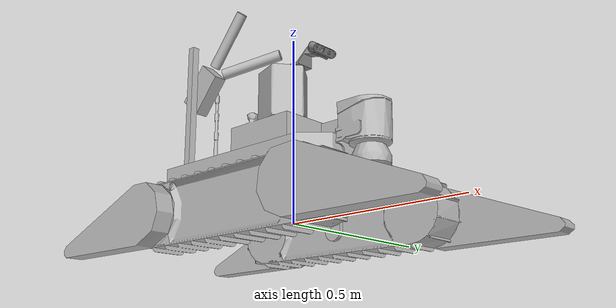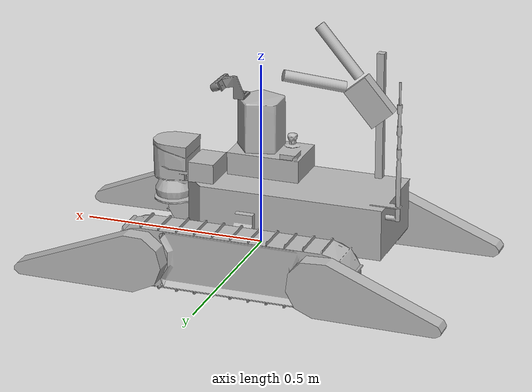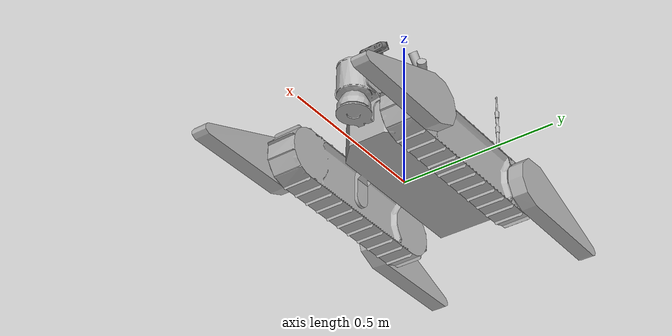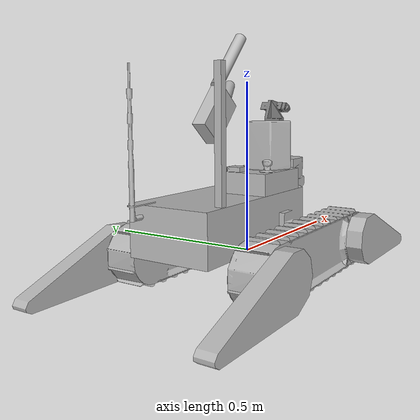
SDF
<?xml version='1.0' encoding='utf-8'?>
<sdf version="1.6">
  <model name="ctu_cras_norlab_absolem_sensor_config_1">
    <link name="base_link">
      <inertial>
        <pose>-0.062088 -0.006779 0.166362 0 -0 0</pose>
        <mass>22.4783</mass>
        <inertia>
          <ixx>0.178253</ixx>
          <ixy>0.0177326</ixy>
          <ixz>-0.0781139</ixz>
          <iyy>0.4196</iyy>
          <iyz>0.0158494</iyz>
          <izz>0.33554</izz>
        </inertia>
      </inertial>
      <collision name="base_link_collision">
        <pose>-0.122 0 0.118 0 -0 0</pose>
        <geometry>
          <box>
            <size>0.50017 0.24093 0.139</size>
          </box>
        </geometry>
      </collision>
      <collision name="base_link_collision_1">
        <pose>0.157 0 0.118 0 -0 0</pose>
        <geometry>
          <box>
            <size>0.056 0.12093 0.139</size>
          </box>
        </geometry>
      </collision>
      <collision name="base_link_collision_2">
        <pose>0.144 -0.076 0.118 0 -0 0.785398</pose>
        <geometry>
          <box>
            <size>0.083 0.04 0.139</size>
          </box>
        </geometry>
      </collision>
      <collision name="base_link_collision_3">
        <pose>0.144 0.076 0.118 0 0 -0.785398</pose>
        <geometry>
          <box>
            <size>0.083 0.04 0.139</size>
          </box>
        </geometry>
      </collision>
      <collision name="base_link_collision_4">
        <pose>0 0.135 0.09 0 -0 0</pose>
        <geometry>
          <box>
            <size>0.055 0.04 0.08</size>
          </box>
        </geometry>
      </collision>
      <collision name="base_link_collision_5">
        <pose>0 0.155 0.013 0 -0 0</pose>
        <geometry>
          <box>
            <size>0.055 0.02 0.075</size>
          </box>
        </geometry>
      </collision>
      <collision name="base_link_collision_6">
        <pose>0 -0.135 0.09 0 -0 0</pose>
        <geometry>
          <box>
            <size>0.055 0.04 0.08</size>
          </box>
        </geometry>
      </collision>
      <collision name="base_link_collision_7">
        <pose>0 -0.155 0.013 0 -0 0</pose>
        <geometry>
          <box>
            <size>0.055 0.02 0.075</size>
          </box>
        </geometry>
      </collision>
      <collision name="base_link_fixed_joint_lump__antenna_collision_8">
        <pose>-0.39064 0.0789 0.1551 0 1.5707963267948966 0</pose>
        <geometry>
          <cylinder>
            <length>0.03718</length>
            <radius>0.008</radius>
          </cylinder>
        </geometry>
      </collision>
      <collision name="base_link_fixed_joint_lump__antenna_collision_9">
        <pose>-0.402 0.0789 0.34563 0 -0 0</pose>
        <geometry>
          <cylinder>
            <length>0.38107</length>
            <radius>0.008</radius>
          </cylinder>
        </geometry>
      </collision>
      <collision name="base_link_fixed_joint_lump__battery_collision_10">
        <pose>-0.2836 -0.0221 0.1132 0 -0 0</pose>
        <geometry>
          <box>
            <size>0.145 0.135 0.082</size>
          </box>
        </geometry>
      </collision>
      <collision name="base_link_fixed_joint_lump__jetson_collision_11">
        <pose>0.136 0.0435 0.2125 0 -0 0</pose>
        <geometry>
          <box>
            <size>0.07 0.1 0.055</size>
          </box>
        </geometry>
      </collision>
      <collision name="base_link_fixed_joint_lump__rear_sensor_item_collision_12">
        <pose>-0.295 -0.1065 0.36 0 -0 0</pose>
        <geometry>
          <box>
            <size>0.02 0.02 0.35</size>
          </box>
        </geometry>
      </collision>
      <collision name="base_link_fixed_joint_lump__mobilicom_collision_13">
        <pose>-0.295121 -0.064 0.385106 -1.56579 -0.858407 -7.3e-05</pose>
        <geometry>
          <box>
            <size>0.2 0.095 0.065</size>
          </box>
        </geometry>
      </collision>
      <collision name="base_link_fixed_joint_lump__mobilicom_antenna_l_collision_14">
        <pose>-0.139117 -0.02338 0.465445 -1.29704 -0.418237 -1.17028</pose>
        <geometry>
          <cylinder>
            <length>0.17</length>
            <radius>0.025</radius>
          </cylinder>
        </geometry>
      </collision>
      <collision name="base_link_fixed_joint_lump__mobilicom_antenna_r_collision_15">
        <pose>-0.193116 -0.064558 0.541453 -0.7124 0.007057 -1.5707963267948966</pose>
        <geometry>
          <cylinder>
            <length>0.17</length>
            <radius>0.025</radius>
          </cylinder>
        </geometry>
      </collision>
      <collision name="base_link_fixed_joint_lump__top_box_collision_16">
        <pose>-0.007 -0.0557 0.2165 0 -0 0</pose>
        <geometry>
          <box>
            <size>0.2 0.133 0.06252</size>
          </box>
        </geometry>
      </collision>
      <collision name="base_link_fixed_joint_lump__top_box_collision_17">
        <pose>-0.07624 -0.01443 0.254 0 -0 0</pose>
        <geometry>
          <box>
            <size>0.044 0.044 0.01303</size>
          </box>
        </geometry>
      </collision>
      <collision name="base_link_fixed_joint_lump__top_box_collision_18">
        <pose>-0.05183 -0.09792 0.26496 0 -0 0</pose>
        <geometry>
          <box>
            <size>0.03732 0.03523 0.03489</size>
          </box>
        </geometry>
      </collision>
      <collision name="base_link_fixed_joint_lump__omnicam_collision_19">
        <pose>0.020991 -0.05685 0.3172 0 0 -0.628319</pose>
        <geometry>
          <cylinder>
            <length>0.137</length>
            <radius>0.068</radius>
          </cylinder>
        </geometry>
      </collision>
      <collision name="base_link_fixed_joint_lump__realsense_holder_part2_collision_20">
        <pose>0.111811 -0.018928 0.440133 0 0.504467 -0.000319</pose>
        <geometry>
          <box>
            <size>0.008 0.075 0.025</size>
          </box>
        </geometry>
      </collision>
      <collision name="base_link_fixed_joint_lump__realsense_holder_part2_collision_21">
        <pose>0.099551 -0.028924 0.4469 0 0.504467 -0.000319</pose>
        <geometry>
          <box>
            <size>0.035 0.01 0.028</size>
          </box>
        </geometry>
      </collision>
      <collision name="base_link_fixed_joint_lump__realsense_holder_part2_collision_22">
        <pose>0.074085 -0.043916 0.415266 -0 0.004467 -0.000319</pose>
        <geometry>
          <box>
            <size>0.035 0.045 0.073</size>
          </box>
        </geometry>
      </collision>
      <collision name="base_link_fixed_joint_lump__camera_link_collision_23">
        <pose>0.125348 -0.010971 0.43571 0.015 0.499467 -0.000319</pose>
        <geometry>
          <box>
            <size>0.02505 0.09 0.025</size>
          </box>
        </geometry>
      </collision>
      <visual name="base_link_visual">
        <geometry>
          <mesh>
            <uri>meshes/body.dae</uri>
          </mesh>
        </geometry>
      </visual>
      <visual name="base_link_fixed_joint_lump__antenna_visual_1">
        <pose>-0.372 0.0789 0.1551 0 -0 0</pose>
        <geometry>
          <mesh>
            <uri>meshes/antenna.dae</uri>
          </mesh>
        </geometry>
      </visual>
      <visual name="base_link_fixed_joint_lump__battery_visual_2">
        <pose>-0.2836 -0.0221 0.0722 0 -0 0</pose>
        <geometry>
          <mesh>
            <uri>meshes/battery.dae</uri>
          </mesh>
        </geometry>
      </visual>
      <visual name="base_link_fixed_joint_lump__jetson_visual_3">
        <pose>0.136 0.0435 0.2125 0 -0 0</pose>
        <geometry>
          <box>
            <size>0.07 0.1 0.055</size>
          </box>
        </geometry>
      </visual>
      <visual name="base_link_fixed_joint_lump__rear_sensor_item_visual_4">
        <pose>-0.295 -0.1065 0.36 0 -0 0</pose>
        <geometry>
          <box>
            <size>0.02 0.02 0.35</size>
          </box>
        </geometry>
      </visual>
      <visual name="base_link_fixed_joint_lump__mobilicom_visual_5">
        <pose>-0.275459 -0.078002 0.407765 -1.56579 -0.858407 -7.3e-05</pose>
        <geometry>
          <box>
            <size>0.12 0.075 0.037</size>
          </box>
        </geometry>
      </visual>
      <visual name="base_link_fixed_joint_lump__mobilicom_antenna_l_visual_6">
        <pose>-0.139117 -0.02338 0.465445 -1.29704 -0.418237 -1.17028</pose>
        <geometry>
          <cylinder>
            <length>0.17</length>
            <radius>0.015</radius>
          </cylinder>
        </geometry>
      </visual>
      <visual name="base_link_fixed_joint_lump__mobilicom_antenna_r_visual_7">
        <pose>-0.193116 -0.064558 0.541453 -0.7124 0.007057 -1.5707963267948966</pose>
        <geometry>
          <cylinder>
            <length>0.17</length>
            <radius>0.015</radius>
          </cylinder>
        </geometry>
      </visual>
      <visual name="base_link_fixed_joint_lump__top_box_visual_8">
        <pose>0.022 -0.0557 0.185 0 -0 0</pose>
        <geometry>
          <mesh>
            <uri>meshes/top_box.dae</uri>
          </mesh>
        </geometry>
      </visual>
      <visual name="base_link_fixed_joint_lump__omnicam_visual_9">
        <pose>0.0243 -0.0574 0.3142 0 0 -0.628319</pose>
        <geometry>
          <mesh>
            <uri>meshes/omnicam.dae</uri>
          </mesh>
        </geometry>
      </visual>
      <visual name="base_link_fixed_joint_lump__realsense_holder_part2_visual_10">
        <pose>0.088136 -0.07392 0.386942 -5e-06 -0.002418 1.57486</pose>
        <geometry>
          <mesh>
            <scale>0.001 0.001 0.001</scale>
            <uri>meshes/d435_holder_combined.stl</uri>
          </mesh>
        </geometry>
        <material>
          <diffuse>0.5 0.5 0.5 1</diffuse>
          <ambient>0.1 0.1 0.1 1</ambient>
        </material>
      </visual>
      <visual name="base_link_fixed_joint_lump__camera_link_visual_11">
        <pose>0.133719 -0.010853 0.422031 2.07031 -0.013167 1.56329</pose>
        <geometry>
          <mesh>
            <uri>meshes/realsense_d435.dae</uri>
          </mesh>
        </geometry>
        <material>
          <diffuse>0.5 0.5 0.5 1</diffuse>
          <ambient>0.1 0.1 0.1 1</ambient>
        </material>
      </visual>
      <light name="light_left" type="spot">
        <pose>0 0.13 0.2 1.5707963267948966 1.5707963267948966 0</pose>
        <attenuation>
          <range>50</range>
          <linear>0</linear>
          <constant>0.1</constant>
          <quadratic>0.0025</quadratic>
        </attenuation>
        <diffuse>0.8 0.8 0.5 1</diffuse>
        <specular>0.8 0.8 0.5 1</specular>
        <spot>
          <inner_angle>2.8</inner_angle>
          <outer_angle>2.9</outer_angle>
          <falloff>1</falloff>
        </spot>
        <direction>1 0 0</direction>
      </light>
      <light name="light_right" type="spot">
        <pose>0 -0.13 0.2 -1.5707963267948966 1.5707963267948966 0</pose>
        <attenuation>
          <range>50</range>
          <linear>0</linear>
          <constant>0.1</constant>
          <quadratic>0.0025</quadratic>
        </attenuation>
        <diffuse>0.8 0.8 0.5 1</diffuse>
        <specular>0.8 0.8 0.5 1</specular>
        <spot>
          <inner_angle>2.8</inner_angle>
          <outer_angle>2.9</outer_angle>
          <falloff>1</falloff>
        </spot>
        <direction>1 0 0</direction>
      </light>
      <light name="light_front_left" type="spot">
        <pose>0.3 0.13 0.2 2.74889 1.5707963267948966 0</pose>
        <attenuation>
          <range>30</range>
          <linear>0</linear>
          <constant>0.2</constant>
          <quadratic>0.0025</quadratic>
        </attenuation>
        <diffuse>0.8 0.8 0.5 1</diffuse>
        <specular>0.8 0.8 0.5 1</specular>
        <spot>
          <inner_angle>1.5</inner_angle>
          <outer_angle>1.6</outer_angle>
          <falloff>1</falloff>
        </spot>
        <direction>1 0 0</direction>
      </light>
      <light name="light_front_right" type="spot">
        <pose>0.3 -0.13 0.2 -2.74889 1.5707963267948966 0</pose>
        <attenuation>
          <range>30</range>
          <linear>0</linear>
          <constant>0.2</constant>
          <quadratic>0.0025</quadratic>
        </attenuation>
        <diffuse>0.8 0.8 0.5 1</diffuse>
        <specular>0.8 0.8 0.5 1</specular>
        <spot>
          <inner_angle>1.5</inner_angle>
          <outer_angle>1.6</outer_angle>
          <falloff>1</falloff>
        </spot>
        <direction>1 0 0</direction>
      </light>
      <light name="light_rear" type="spot">
        <pose>-0.4 0 0.2 0 1.5707963267948966 0</pose>
        <attenuation>
          <range>30</range>
          <linear>0</linear>
          <constant>0.2</constant>
          <quadratic>0.0025</quadratic>
        </attenuation>
        <diffuse>0.8 0.8 0.5 1</diffuse>
        <specular>0.8 0.8 0.5 1</specular>
        <spot>
          <inner_angle>1.5</inner_angle>
          <outer_angle>1.8</outer_angle>
          <falloff>1</falloff>
        </spot>
        <direction>1 0 0</direction>
      </light>
      <self_collide>0</self_collide>
      <sensor name="imu" type="imu">
        <always_on>1</always_on>
        <update_rate>50</update_rate>
        <imu>
          <enable_orientation>0</enable_orientation>
          <angular_velocity>
            <x>
              <noise type="gaussian">
                <mean>0</mean>
                <stddev>0.009</stddev>
                <bias_mean>0.00075</bias_mean>
                <bias_stddev>0.005</bias_stddev>
                <dynamic_bias_stddev>2e-05</dynamic_bias_stddev>
                <dynamic_bias_correlation_time>400</dynamic_bias_correlation_time>
                <precision>0.00025</precision>
              </noise>
            </x>
            <y>
              <noise type="gaussian">
                <mean>0</mean>
                <stddev>0.009</stddev>
                <bias_mean>0.00075</bias_mean>
                <bias_stddev>0.005</bias_stddev>
                <dynamic_bias_stddev>2e-05</dynamic_bias_stddev>
                <dynamic_bias_correlation_time>400</dynamic_bias_correlation_time>
                <precision>0.00025</precision>
              </noise>
            </y>
            <z>
              <noise type="gaussian">
                <mean>0</mean>
                <stddev>0.009</stddev>
                <bias_mean>0.00075</bias_mean>
                <bias_stddev>0.005</bias_stddev>
                <dynamic_bias_stddev>2e-05</dynamic_bias_stddev>
                <dynamic_bias_correlation_time>400</dynamic_bias_correlation_time>
                <precision>0.00025</precision>
              </noise>
            </z>
          </angular_velocity>
          <linear_acceleration>
            <x>
              <noise type="gaussian">
                <mean>0</mean>
                <stddev>0.021</stddev>
                <bias_mean>0.05</bias_mean>
                <bias_stddev>0.0075</bias_stddev>
                <dynamic_bias_stddev>0.000375</dynamic_bias_stddev>
                <dynamic_bias_correlation_time>175</dynamic_bias_correlation_time>
                <precision>0.005</precision>
              </noise>
            </x>
            <y>
              <noise type="gaussian">
                <mean>0</mean>
                <stddev>0.021</stddev>
                <bias_mean>0.05</bias_mean>
                <bias_stddev>0.0075</bias_stddev>
                <dynamic_bias_stddev>0.000375</dynamic_bias_stddev>
                <dynamic_bias_correlation_time>175</dynamic_bias_correlation_time>
                <precision>0.005</precision>
              </noise>
            </y>
            <z>
              <noise type="gaussian">
                <mean>0</mean>
                <stddev>0.021</stddev>
                <bias_mean>0.05</bias_mean>
                <bias_stddev>0.0075</bias_stddev>
                <dynamic_bias_stddev>0.000375</dynamic_bias_stddev>
                <dynamic_bias_correlation_time>175</dynamic_bias_correlation_time>
                <precision>0.005</precision>
              </noise>
            </z>
          </linear_acceleration>
        </imu>
        <pose>0 0 0.15 -3.1415926535897931 -0 0</pose>
      </sensor>
      <sensor name="omnicam_sensor0" type="camera">
        <update_rate>6</update_rate>
        <camera name="camera_0">
          <horizontal_fov>1.36478</horizontal_fov>
          <image>
            <width>1232</width>
            <height>1616</height>
            <format>R8G8B8</format>
          </image>
          <clip>
            <near>0.02</near>
            <far>300</far>
          </clip>
          <noise>
            <type>gaussian</type>
            <mean>0</mean>
            <stddev>0.007</stddev>
          </noise>
          <distortion>
            <k1>-0.20571</k1>
            <k2>0.04103</k2>
            <k3>0</k3>
            <p1>-0.00101</p1>
            <p2>0.00098</p2>
          </distortion>
          <lens>
            <intrinsics>
              <fx>758.04</fx>
              <fy>761.624</fy>
              <cx>621.466</cx>
              <cy>756.864</cy>
              <s>1</s>
            </intrinsics>
            <type>stereographic</type>
            <scale_to_hfov>1</scale_to_hfov>
          </lens>
        </camera>
        <pose>0.057346 -0.083518 0.313841 -0.000948 -0.000784 -2.19802</pose>
      </sensor>
      <sensor name="omnicam_sensor1" type="camera">
        <update_rate>6</update_rate>
        <camera name="camera_1">
          <horizontal_fov>1.36574</horizontal_fov>
          <image>
            <width>1232</width>
            <height>1616</height>
            <format>R8G8B8</format>
          </image>
          <clip>
            <near>0.02</near>
            <far>300</far>
          </clip>
          <noise>
            <type>gaussian</type>
            <mean>0</mean>
            <stddev>0.007</stddev>
          </noise>
          <distortion>
            <k1>-0.19931</k1>
            <k2>0.03549</k2>
            <k3>0</k3>
            <p1>5e-05</p1>
            <p2>-0.00053</p2>
          </distortion>
          <lens>
            <intrinsics>
              <fx>757.299</fx>
              <fy>757.801</fy>
              <cx>594.19</cx>
              <cy>779.434</cy>
              <s>1</s>
            </intrinsics>
            <type>stereographic</type>
            <scale_to_hfov>1</scale_to_hfov>
          </lens>
        </camera>
        <pose>0.009992 -0.096606 0.314114 -0.001069 0.000853 2.82791</pose>
      </sensor>
      <sensor name="omnicam_sensor2" type="camera">
        <update_rate>6</update_rate>
        <camera name="camera_2">
          <horizontal_fov>1.36565</horizontal_fov>
          <image>
            <width>1232</width>
            <height>1616</height>
            <format>R8G8B8</format>
          </image>
          <clip>
            <near>0.02</near>
            <far>300</far>
          </clip>
          <noise>
            <type>gaussian</type>
            <mean>0</mean>
            <stddev>0.007</stddev>
          </noise>
          <distortion>
            <k1>-0.19722</k1>
            <k2>0.03442</k2>
            <k3>0</k3>
            <p1>0.00013</p1>
            <p2>-0.00035</p2>
          </distortion>
          <lens>
            <intrinsics>
              <fx>757.367</fx>
              <fy>755.079</fy>
              <cx>632.96</cx>
              <cy>740.558</cy>
              <s>1</s>
            </intrinsics>
            <type>stereographic</type>
            <scale_to_hfov>1</scale_to_hfov>
          </lens>
        </camera>
        <pose>-0.01735 -0.055429 0.314721 -0.001705 0.00415 1.56975</pose>
      </sensor>
      <sensor name="omnicam_sensor3" type="camera">
        <update_rate>6</update_rate>
        <camera name="camera_3">
          <horizontal_fov>1.35821</horizontal_fov>
          <image>
            <width>1232</width>
            <height>1616</height>
            <format>R8G8B8</format>
          </image>
          <clip>
            <near>0.02</near>
            <far>300</far>
          </clip>
          <noise>
            <type>gaussian</type>
            <mean>0</mean>
            <stddev>0.007</stddev>
          </noise>
          <distortion>
            <k1>-0.20395</k1>
            <k2>0.03534</k2>
            <k3>0</k3>
            <p1>0.0003</p1>
            <p2>-0.00066</p2>
          </distortion>
          <lens>
            <intrinsics>
              <fx>763.152</fx>
              <fy>763.185</fy>
              <cx>606.706</cx>
              <cy>785.217</cy>
              <s>1</s>
            </intrinsics>
            <type>stereographic</type>
            <scale_to_hfov>1</scale_to_hfov>
          </lens>
        </camera>
        <pose>0.012561 -0.017068 0.314417 -0.000579 0.005611 0.313689</pose>
      </sensor>
      <sensor name="omnicam_sensor4" type="camera">
        <update_rate>6</update_rate>
        <camera name="camera_4">
          <horizontal_fov>1.37789</horizontal_fov>
          <image>
            <width>1232</width>
            <height>1616</height>
            <format>R8G8B8</format>
          </image>
          <clip>
            <near>0.02</near>
            <far>300</far>
          </clip>
          <noise>
            <type>gaussian</type>
            <mean>0</mean>
            <stddev>0.007</stddev>
          </noise>
          <distortion>
            <k1>-0.19889</k1>
            <k2>0.03244</k2>
            <k3>0</k3>
            <p1>-0.00039</p1>
            <p2>-0.00126</p2>
          </distortion>
          <lens>
            <intrinsics>
              <fx>747.97</fx>
              <fy>744.851</fy>
              <cx>612.798</cx>
              <cy>772.008</cy>
              <s>1</s>
            </intrinsics>
            <type>stereographic</type>
            <scale_to_hfov>1</scale_to_hfov>
          </lens>
        </camera>
        <pose>0.058951 -0.03438 0.313899 -0.010815 0.001034 -0.943109</pose>
      </sensor>
      <sensor name="omnicam_sensor5" type="camera">
        <update_rate>6</update_rate>
        <camera name="camera_5">
          <horizontal_fov>1.36869</horizontal_fov>
          <image>
            <width>1232</width>
            <height>1616</height>
            <format>R8G8B8</format>
          </image>
          <clip>
            <near>0.02</near>
            <far>300</far>
          </clip>
          <noise>
            <type>gaussian</type>
            <mean>0</mean>
            <stddev>0.007</stddev>
          </noise>
          <distortion>
            <k1>-0.21309</k1>
            <k2>0.03984</k2>
            <k3>0</k3>
            <p1>-0.00011</p1>
            <p2>-0.00017</p2>
          </distortion>
          <lens>
            <intrinsics>
              <fx>755.019</fx>
              <fy>754.96</fy>
              <cx>602.194</cx>
              <cy>802.92</cy>
              <s>1</s>
            </intrinsics>
            <type>stereographic</type>
            <scale_to_hfov>1</scale_to_hfov>
          </lens>
        </camera>
        <pose>0.024083 -0.058382 0.376328 3.1415926535897931 -1.5707963267948966 0.945143</pose>
      </sensor>
      <sensor name="camera" type="rgbd_camera">
        <camera name="camera_camera">
          <horizontal_fov>1.5184</horizontal_fov>
          <lens>
            <intrinsics>
              <fx>337.222</fx>
              <fy>337.222</fy>
              <cx>320.5</cx>
              <cy>240.5</cy>
              <s>0</s>
            </intrinsics>
            <type>stereographic</type>
            <scale_to_hfov>1</scale_to_hfov>
          </lens>
          <distortion>
            <k1>0</k1>
            <k2>0</k2>
            <k3>0</k3>
            <p1>0</p1>
            <p2>0</p2>
            <center>0.5 0.5</center>
          </distortion>
          <image>
            <width>640</width>
            <height>480</height>
            <format>RGB_INT8</format>
          </image>
          <clip>
            <near>0.01</near>
            <far>100</far>
          </clip>
          <depth_camera>
            <clip>
              <near>0.1</near>
              <far>10</far>
            </clip>
            <output>depths</output>
          </depth_camera>
          <noise>
            <type>gaussian</type>
            <mean>0</mean>
            <stddev>0.007</stddev>
          </noise>
        </camera>
        <always_on>1</always_on>
        <update_rate>6</update_rate>
        <pose>0.13592 -0.016338 0.419596 0.015 0.499467 -0.000319</pose>
      </sensor>
    </link>
    <link name="laser">
      <pose>0.2502 0 0.1407 -3.1415926535897931 0 0</pose>
      <inertial>
        <pose>0 0 -0.04 0 -0 0</pose>
        <mass>1.1</mass>
        <inertia>
          <ixx>0.0031194</ixx>
          <ixy>-2.221e-06</ixy>
          <ixz>-1.1577e-06</ixz>
          <iyy>0.0031389</iyy>
          <iyz>-1.153e-05</iyz>
          <izz>0.0017656</izz>
        </inertia>
      </inertial>
      <collision name="laser_collision">
        <pose>0 0 -0.04 1.5707963267948966 0 -1.5707963267948966</pose>
        <geometry>
          <box>
            <size>0.1159 0.16826 0.1159</size>
          </box>
        </geometry>
      </collision>
      <visual name="laser_visual">
        <pose>0 0 0 1.5707963267948966 0 -1.5707963267948966</pose>
        <geometry>
          <mesh>
            <uri>meshes/laser.dae</uri>
          </mesh>
        </geometry>
      </visual>
      <sensor name="laser" type="gpu_lidar">
        <update_rate>50</update_rate>
        <always_on>1</always_on>
        <lidar>
          <scan>
            <horizontal>
              <samples>541</samples>
              <resolution>1</resolution>
              <min_angle>-2.35619</min_angle>
              <max_angle>2.35619</max_angle>
            </horizontal>
          </scan>
          <range>
            <min>0.2</min>
            <max>50</max>
            <resolution>0.01</resolution>
          </range>
          <noise>
            <type>gaussian</type>
            <mean>0</mean>
            <stddev>0.01</stddev>
          </noise>
        </lidar>
      </sensor>
    </link>
    <joint name="laser_j" type="revolute">
      <child>laser</child>
      <parent>base_link</parent>
      <axis>
        <xyz>1 0 0</xyz>
        <limit>
          <lower>-2.35619</lower>
          <upper>2.35619</upper>
          <effort>10</effort>
          <velocity>1.2</velocity>
        </limit>
        <dynamics>
          <spring_reference>0</spring_reference>
          <spring_stiffness>0</spring_stiffness>
        </dynamics>
        <use_parent_model_frame>0</use_parent_model_frame>
      </axis>
      <physics>
        <ode>
          <implicit_spring_damper>1</implicit_spring_damper>
          <cfm_damping>1</cfm_damping>
          <limit>
            <cfm>0</cfm>
            <erp>0.2</erp>
          </limit>
        </ode>
      </physics>
    </joint>
    <link name="left_track">
      <pose>0 0.1985 0 0 -0 0</pose>
      <inertial>
        <mass>1e-05</mass>
        <inertia>
          <ixx>0.001</ixx>
          <ixy>1e-06</ixy>
          <ixz>1e-06</ixz>
          <iyy>0.001</iyy>
          <iyz>1e-06</iyz>
          <izz>0.001</izz>
        </inertia>
      </inertial>
      <collision name="left_track_collision">
        <geometry>
          <box>
            <size>0.01 0.01 0.01</size>
          </box>
        </geometry>
        <surface>
          <friction>
            <ode>
              <mu>0.7</mu>
              <mu2>150</mu2>
              <fdir1>0 0 1</fdir1>
            </ode>
          </friction>
        </surface>
      </collision>
      <visual name="left_track_visual">
        <pose>0 0 -0.0705 1.5707963267948966 -0 1.5707963267948966</pose>
        <geometry>
          <mesh>
            <uri>meshes/bogie.dae</uri>
          </mesh>
        </geometry>
      </visual>
    </link>
    <joint name="left_track_j" type="revolute">
      <child>left_track</child>
      <parent>base_link</parent>
      <axis>
        <xyz>0 1 0</xyz>
        <limit>
          <lower>0</lower>
          <upper>0</upper>
          <effort>0</effort>
          <velocity>4</velocity>
        </limit>
        <dynamics>
          <spring_reference>0</spring_reference>
          <spring_stiffness>0</spring_stiffness>
        </dynamics>
        <use_parent_model_frame>0</use_parent_model_frame>
      </axis>
      <physics>
        <ode>
          <limit>
            <cfm>0</cfm>
            <erp>0.2</erp>
          </limit>
        </ode>
      </physics>
      <physics>
        <ode>
          <implicit_spring_damper>1</implicit_spring_damper>
          <cfm>0</cfm>
          <erp>0.95</erp>
        </ode>
      </physics>
    </joint>
    <link name="front_left_flipper">
      <pose>0.25 0.272 0.0195 0 0.193732 0</pose>
      <inertial>
        <mass>1e-05</mass>
        <inertia>
          <ixx>0.001</ixx>
          <ixy>1e-06</ixy>
          <ixz>1e-06</ixz>
          <iyy>0.001</iyy>
          <iyz>1e-06</iyz>
          <izz>0.001</izz>
        </inertia>
      </inertial>
      <collision name="front_left_flipper_collision">
        <geometry>
          <box>
            <size>0.01 0.01 0.01</size>
          </box>
        </geometry>
        <surface>
          <friction>
            <ode>
              <mu>0.7</mu>
              <mu2>150</mu2>
              <fdir1>0 0 1</fdir1>
            </ode>
          </friction>
        </surface>
      </collision>
      <visual name="front_left_flipper_visual">
        <pose>0 0 0 -2.95743 -0 1.5707963267948966</pose>
        <geometry>
          <mesh>
            <uri>meshes/flipper.dae</uri>
          </mesh>
        </geometry>
      </visual>
    </link>
    <joint name="front_left_flipper_j" type="revolute">
      <child>front_left_flipper</child>
      <parent>left_track</parent>
      <axis>
        <xyz>0 1 0</xyz>
        <limit>
          <lower>-1e+16</lower>
          <upper>1e+16</upper>
          <effort>20</effort>
          <velocity>0.785398</velocity>
        </limit>
        <dynamics>
          <spring_reference>0</spring_reference>
          <spring_stiffness>0</spring_stiffness>
        </dynamics>
        <use_parent_model_frame>0</use_parent_model_frame>
      </axis>
      <physics>
        <ode>
          <implicit_spring_damper>1</implicit_spring_damper>
          <cfm_damping>1</cfm_damping>
          <limit>
            <cfm>0</cfm>
            <erp>0.2</erp>
          </limit>
        </ode>
      </physics>
    </joint>
    <link name="front_left_flipper_wheel1">
      <pose>0.25 0.272 0.0195 0 0.193732 0</pose>
      <inertial>
        <pose>0.08 0 0 0 -0 0</pose>
        <mass>0.15</mass>
        <inertia>
          <ixx>0.0017491</ixx>
          <ixy>2.8512e-07</ixy>
          <ixz>0.0018277</ixz>
          <iyy>0.012277</iyy>
          <iyz>-3.6288e-07</iyz>
          <izz>0.010941</izz>
        </inertia>
      </inertial>
      <collision name="front_left_flipper_wheel1_collision_collision">
        <pose>0 0 0 1.5707963267948966 -0 0</pose>
        <geometry>
          <cylinder>
            <length>0.04981</length>
            <radius>0.089</radius>
          </cylinder>
        </geometry>
        <surface>
          <contact>
            <ode>
              <kp>1e+07</kp>
              <kd>1</kd>
            </ode>
          </contact>
          <friction>
            <ode>
              <mu>0.5</mu>
              <mu2>1</mu2>
              <slip1>0.00092</slip1>
              <slip2>0</slip2>
              <fdir1>0 0 1</fdir1>
            </ode>
          </friction>
        </surface>
      </collision>
    </link>
    <joint name="front_left_flipper_wheel1_j" type="revolute">
      <child>front_left_flipper_wheel1</child>
      <parent>front_left_flipper</parent>
      <axis>
        <xyz>0 1 0</xyz>
        <limit>
          <lower>-1e+16</lower>
          <upper>1e+16</upper>
        </limit>
        <dynamics>
          <spring_reference>0</spring_reference>
          <spring_stiffness>0</spring_stiffness>
        </dynamics>
        <use_parent_model_frame>0</use_parent_model_frame>
      </axis>
    </joint>
    <link name="front_left_flipper_wheel2">
      <pose>0.330957 0.272 0.003617 0 0.193732 0</pose>
      <inertial>
        <pose>0.08 0 0 0 -0 0</pose>
        <mass>0.15</mass>
        <inertia>
          <ixx>0.0017491</ixx>
          <ixy>2.8512e-07</ixy>
          <ixz>0.0018277</ixz>
          <iyy>0.012277</iyy>
          <iyz>-3.6288e-07</iyz>
          <izz>0.010941</izz>
        </inertia>
      </inertial>
      <collision name="front_left_flipper_wheel2_collision_collision">
        <pose>0 0 0 1.5707963267948966 -0 0</pose>
        <geometry>
          <cylinder>
            <length>0.04981</length>
            <radius>0.074</radius>
          </cylinder>
        </geometry>
        <surface>
          <contact>
            <ode>
              <kp>1e+07</kp>
              <kd>1</kd>
            </ode>
          </contact>
          <friction>
            <ode>
              <mu>0.5</mu>
              <mu2>1</mu2>
              <slip1>0.00092</slip1>
              <slip2>0</slip2>
              <fdir1>0 0 1</fdir1>
            </ode>
          </friction>
        </surface>
      </collision>
    </link>
    <joint name="front_left_flipper_wheel2_j" type="revolute">
      <child>front_left_flipper_wheel2</child>
      <parent>front_left_flipper</parent>
      <axis>
        <xyz>0 1 0</xyz>
        <limit>
          <lower>-1e+16</lower>
          <upper>1e+16</upper>
        </limit>
        <dynamics>
          <spring_reference>0</spring_reference>
          <spring_stiffness>0</spring_stiffness>
        </dynamics>
        <use_parent_model_frame>0</use_parent_model_frame>
      </axis>
    </joint>
    <link name="front_left_flipper_wheel3">
      <pose>0.411913 0.272 -0.012266 0 0.193732 0</pose>
      <inertial>
        <pose>0.08 0 0 0 -0 0</pose>
        <mass>0.15</mass>
        <inertia>
          <ixx>0.0017491</ixx>
          <ixy>2.8512e-07</ixy>
          <ixz>0.0018277</ixz>
          <iyy>0.012277</iyy>
          <iyz>-3.6288e-07</iyz>
          <izz>0.010941</izz>
        </inertia>
      </inertial>
      <collision name="front_left_flipper_wheel3_collision_collision">
        <pose>0 0 0 1.5707963267948966 -0 0</pose>
        <geometry>
          <cylinder>
            <length>0.04981</length>
            <radius>0.059</radius>
          </cylinder>
        </geometry>
        <surface>
          <contact>
            <ode>
              <kp>1e+07</kp>
              <kd>1</kd>
            </ode>
          </contact>
          <friction>
            <ode>
              <mu>0.5</mu>
              <mu2>1</mu2>
              <slip1>0.00092</slip1>
              <slip2>0</slip2>
              <fdir1>0 0 1</fdir1>
            </ode>
          </friction>
        </surface>
      </collision>
    </link>
    <joint name="front_left_flipper_wheel3_j" type="revolute">
      <child>front_left_flipper_wheel3</child>
      <parent>front_left_flipper</parent>
      <axis>
        <xyz>0 1 0</xyz>
        <limit>
          <lower>-1e+16</lower>
          <upper>1e+16</upper>
        </limit>
        <dynamics>
          <spring_reference>0</spring_reference>
          <spring_stiffness>0</spring_stiffness>
        </dynamics>
        <use_parent_model_frame>0</use_parent_model_frame>
      </axis>
    </joint>
    <link name="front_left_flipper_wheel4">
      <pose>0.49287 0.272 -0.028149 0 0.193732 0</pose>
      <inertial>
        <pose>0.08 0 0 0 -0 0</pose>
        <mass>0.15</mass>
        <inertia>
          <ixx>0.0017491</ixx>
          <ixy>2.8512e-07</ixy>
          <ixz>0.0018277</ixz>
          <iyy>0.012277</iyy>
          <iyz>-3.6288e-07</iyz>
          <izz>0.010941</izz>
        </inertia>
      </inertial>
      <collision name="front_left_flipper_wheel4_collision_collision">
        <pose>0 0 0 1.5707963267948966 -0 0</pose>
        <geometry>
          <cylinder>
            <length>0.04981</length>
            <radius>0.044</radius>
          </cylinder>
        </geometry>
        <surface>
          <contact>
            <ode>
              <kp>1e+07</kp>
              <kd>1</kd>
            </ode>
          </contact>
          <friction>
            <ode>
              <mu>0.5</mu>
              <mu2>1</mu2>
              <slip1>0.00092</slip1>
              <slip2>0</slip2>
              <fdir1>0 0 1</fdir1>
            </ode>
          </friction>
        </surface>
      </collision>
    </link>
    <joint name="front_left_flipper_wheel4_j" type="revolute">
      <child>front_left_flipper_wheel4</child>
      <parent>front_left_flipper</parent>
      <axis>
        <xyz>0 1 0</xyz>
        <limit>
          <lower>-1e+16</lower>
          <upper>1e+16</upper>
        </limit>
        <dynamics>
          <spring_reference>0</spring_reference>
          <spring_stiffness>0</spring_stiffness>
        </dynamics>
        <use_parent_model_frame>0</use_parent_model_frame>
      </axis>
    </joint>
    <link name="front_left_flipper_wheel5">
      <pose>0.573827 0.272 -0.044032 0 0.193732 0</pose>
      <inertial>
        <pose>0.08 0 0 0 -0 0</pose>
        <mass>0.15</mass>
        <inertia>
          <ixx>0.0017491</ixx>
          <ixy>2.8512e-07</ixy>
          <ixz>0.0018277</ixz>
          <iyy>0.012277</iyy>
          <iyz>-3.6288e-07</iyz>
          <izz>0.010941</izz>
        </inertia>
      </inertial>
      <collision name="front_left_flipper_wheel5_collision_collision">
        <pose>0 0 0 1.5707963267948966 -0 0</pose>
        <geometry>
          <cylinder>
            <length>0.04981</length>
            <radius>0.029</radius>
          </cylinder>
        </geometry>
        <surface>
          <contact>
            <ode>
              <kp>1e+07</kp>
              <kd>1</kd>
            </ode>
          </contact>
          <friction>
            <ode>
              <mu>0.5</mu>
              <mu2>1</mu2>
              <slip1>0.00092</slip1>
              <slip2>0</slip2>
              <fdir1>0 0 1</fdir1>
            </ode>
          </friction>
        </surface>
      </collision>
    </link>
    <joint name="front_left_flipper_wheel5_j" type="revolute">
      <child>front_left_flipper_wheel5</child>
      <parent>front_left_flipper</parent>
      <axis>
        <xyz>0 1 0</xyz>
        <limit>
          <lower>-1e+16</lower>
          <upper>1e+16</upper>
        </limit>
        <dynamics>
          <spring_reference>0</spring_reference>
          <spring_stiffness>0</spring_stiffness>
        </dynamics>
        <use_parent_model_frame>0</use_parent_model_frame>
      </axis>
    </joint>
    <link name="left_track_wheel1">
      <pose>0.25 0.1985 0.01855 0 -0 0</pose>
      <inertial>
        <pose>0 0 0.0141 0 -0 0</pose>
        <mass>0.7575</mass>
        <inertia>
          <ixx>0.002731</ixx>
          <ixy>0</ixy>
          <ixz>0</ixz>
          <iyy>0.032554</iyy>
          <iyz>1.5e-05</iyz>
          <izz>0.031391</izz>
        </inertia>
      </inertial>
      <collision name="left_track_wheel1_collision">
        <pose>0 -0.015 0 1.5707963267948966 -0 0</pose>
        <geometry>
          <cylinder>
            <length>0.112</length>
            <radius>0.089</radius>
          </cylinder>
        </geometry>
        <surface>
          <contact>
            <ode>
              <kp>1e+07</kp>
              <kd>1</kd>
            </ode>
          </contact>
          <friction>
            <ode>
              <mu>0.5</mu>
              <mu2>1</mu2>
              <slip1>0.00092</slip1>
              <slip2>0</slip2>
              <fdir1>0 0 1</fdir1>
            </ode>
          </friction>
        </surface>
      </collision>
    </link>
    <joint name="left_track_wheel1_j" type="revolute">
      <child>left_track_wheel1</child>
      <parent>left_track</parent>
      <axis>
        <xyz>0 1 0</xyz>
        <limit>
          <lower>-1e+16</lower>
          <upper>1e+16</upper>
        </limit>
        <dynamics>
          <spring_reference>0</spring_reference>
          <spring_stiffness>0</spring_stiffness>
        </dynamics>
        <use_parent_model_frame>0</use_parent_model_frame>
      </axis>
    </joint>
    <link name="left_track_wheel2">
      <pose>0.178571 0.1985 0.01855 0 -0 0</pose>
      <inertial>
        <pose>0 0 0.0141 0 -0 0</pose>
        <mass>0.7575</mass>
        <inertia>
          <ixx>0.002731</ixx>
          <ixy>0</ixy>
          <ixz>0</ixz>
          <iyy>0.032554</iyy>
          <iyz>1.5e-05</iyz>
          <izz>0.031391</izz>
        </inertia>
      </inertial>
      <collision name="left_track_wheel2_collision">
        <pose>0 0 0 1.5707963267948966 -0 0</pose>
        <geometry>
          <cylinder>
            <length>0.097</length>
            <radius>0.089</radius>
          </cylinder>
        </geometry>
        <surface>
          <contact>
            <ode>
              <kp>1e+07</kp>
              <kd>1</kd>
            </ode>
          </contact>
          <friction>
            <ode>
              <mu>0.5</mu>
              <mu2>1</mu2>
              <slip1>0.00092</slip1>
              <slip2>0</slip2>
              <fdir1>0 0 1</fdir1>
            </ode>
          </friction>
        </surface>
      </collision>
    </link>
    <joint name="left_track_wheel2_j" type="revolute">
      <child>left_track_wheel2</child>
      <parent>left_track</parent>
      <axis>
        <xyz>0 1 0</xyz>
        <limit>
          <lower>-1e+16</lower>
          <upper>1e+16</upper>
        </limit>
        <dynamics>
          <spring_reference>0</spring_reference>
          <spring_stiffness>0</spring_stiffness>
        </dynamics>
        <use_parent_model_frame>0</use_parent_model_frame>
      </axis>
    </joint>
    <link name="left_track_wheel3">
      <pose>0.107143 0.1985 0.01855 0 -0 0</pose>
      <inertial>
        <pose>0 0 0.0141 0 -0 0</pose>
        <mass>0.7575</mass>
        <inertia>
          <ixx>0.002731</ixx>
          <ixy>0</ixy>
          <ixz>0</ixz>
          <iyy>0.032554</iyy>
          <iyz>1.5e-05</iyz>
          <izz>0.031391</izz>
        </inertia>
      </inertial>
      <collision name="left_track_wheel3_collision">
        <pose>0 0 0 1.5707963267948966 -0 0</pose>
        <geometry>
          <cylinder>
            <length>0.097</length>
            <radius>0.089</radius>
          </cylinder>
        </geometry>
        <surface>
          <contact>
            <ode>
              <kp>1e+07</kp>
              <kd>1</kd>
            </ode>
          </contact>
          <friction>
            <ode>
              <mu>0.5</mu>
              <mu2>1</mu2>
              <slip1>0.00092</slip1>
              <slip2>0</slip2>
              <fdir1>0 0 1</fdir1>
            </ode>
          </friction>
        </surface>
      </collision>
    </link>
    <joint name="left_track_wheel3_j" type="revolute">
      <child>left_track_wheel3</child>
      <parent>left_track</parent>
      <axis>
        <xyz>0 1 0</xyz>
        <limit>
          <lower>-1e+16</lower>
          <upper>1e+16</upper>
        </limit>
        <dynamics>
          <spring_reference>0</spring_reference>
          <spring_stiffness>0</spring_stiffness>
        </dynamics>
        <use_parent_model_frame>0</use_parent_model_frame>
      </axis>
    </joint>
    <link name="left_track_wheel4">
      <pose>0.035714 0.1985 0.01855 0 -0 0</pose>
      <inertial>
        <pose>0 0 0.0141 0 -0 0</pose>
        <mass>0.7575</mass>
        <inertia>
          <ixx>0.002731</ixx>
          <ixy>0</ixy>
          <ixz>0</ixz>
          <iyy>0.032554</iyy>
          <iyz>1.5e-05</iyz>
          <izz>0.031391</izz>
        </inertia>
      </inertial>
      <collision name="left_track_wheel4_collision">
        <pose>0 0 0 1.5707963267948966 -0 0</pose>
        <geometry>
          <cylinder>
            <length>0.097</length>
            <radius>0.089</radius>
          </cylinder>
        </geometry>
        <surface>
          <contact>
            <ode>
              <kp>1e+07</kp>
              <kd>1</kd>
            </ode>
          </contact>
          <friction>
            <ode>
              <mu>0.5</mu>
              <mu2>1</mu2>
              <slip1>0.00092</slip1>
              <slip2>0</slip2>
              <fdir1>0 0 1</fdir1>
            </ode>
          </friction>
        </surface>
      </collision>
    </link>
    <joint name="left_track_wheel4_j" type="revolute">
      <child>left_track_wheel4</child>
      <parent>left_track</parent>
      <axis>
        <xyz>0 1 0</xyz>
        <limit>
          <lower>-1e+16</lower>
          <upper>1e+16</upper>
        </limit>
        <dynamics>
          <spring_reference>0</spring_reference>
          <spring_stiffness>0</spring_stiffness>
        </dynamics>
        <use_parent_model_frame>0</use_parent_model_frame>
      </axis>
    </joint>
    <link name="left_track_wheel5">
      <pose>-0.035714 0.1985 0.01855 0 -0 0</pose>
      <inertial>
        <pose>0 0 0.0141 0 -0 0</pose>
        <mass>0.7575</mass>
        <inertia>
          <ixx>0.002731</ixx>
          <ixy>0</ixy>
          <ixz>0</ixz>
          <iyy>0.032554</iyy>
          <iyz>1.5e-05</iyz>
          <izz>0.031391</izz>
        </inertia>
      </inertial>
      <collision name="left_track_wheel5_collision">
        <pose>0 0 0 1.5707963267948966 -0 0</pose>
        <geometry>
          <cylinder>
            <length>0.097</length>
            <radius>0.089</radius>
          </cylinder>
        </geometry>
        <surface>
          <contact>
            <ode>
              <kp>1e+07</kp>
              <kd>1</kd>
            </ode>
          </contact>
          <friction>
            <ode>
              <mu>0.5</mu>
              <mu2>1</mu2>
              <slip1>0.00092</slip1>
              <slip2>0</slip2>
              <fdir1>0 0 1</fdir1>
            </ode>
          </friction>
        </surface>
      </collision>
    </link>
    <joint name="left_track_wheel5_j" type="revolute">
      <child>left_track_wheel5</child>
      <parent>left_track</parent>
      <axis>
        <xyz>0 1 0</xyz>
        <limit>
          <lower>-1e+16</lower>
          <upper>1e+16</upper>
        </limit>
        <dynamics>
          <spring_reference>0</spring_reference>
          <spring_stiffness>0</spring_stiffness>
        </dynamics>
        <use_parent_model_frame>0</use_parent_model_frame>
      </axis>
    </joint>
    <link name="left_track_wheel6">
      <pose>-0.107143 0.1985 0.01855 0 -0 0</pose>
      <inertial>
        <pose>0 0 0.0141 0 -0 0</pose>
        <mass>0.7575</mass>
        <inertia>
          <ixx>0.002731</ixx>
          <ixy>0</ixy>
          <ixz>0</ixz>
          <iyy>0.032554</iyy>
          <iyz>1.5e-05</iyz>
          <izz>0.031391</izz>
        </inertia>
      </inertial>
      <collision name="left_track_wheel6_collision">
        <pose>0 0 0 1.5707963267948966 -0 0</pose>
        <geometry>
          <cylinder>
            <length>0.097</length>
            <radius>0.089</radius>
          </cylinder>
        </geometry>
        <surface>
          <contact>
            <ode>
              <kp>1e+07</kp>
              <kd>1</kd>
            </ode>
          </contact>
          <friction>
            <ode>
              <mu>0.5</mu>
              <mu2>1</mu2>
              <slip1>0.00092</slip1>
              <slip2>0</slip2>
              <fdir1>0 0 1</fdir1>
            </ode>
          </friction>
        </surface>
      </collision>
    </link>
    <joint name="left_track_wheel6_j" type="revolute">
      <child>left_track_wheel6</child>
      <parent>left_track</parent>
      <axis>
        <xyz>0 1 0</xyz>
        <limit>
          <lower>-1e+16</lower>
          <upper>1e+16</upper>
        </limit>
        <dynamics>
          <spring_reference>0</spring_reference>
          <spring_stiffness>0</spring_stiffness>
        </dynamics>
        <use_parent_model_frame>0</use_parent_model_frame>
      </axis>
    </joint>
    <link name="left_track_wheel7">
      <pose>-0.178571 0.1985 0.01855 0 -0 0</pose>
      <inertial>
        <pose>0 0 0.0141 0 -0 0</pose>
        <mass>0.7575</mass>
        <inertia>
          <ixx>0.002731</ixx>
          <ixy>0</ixy>
          <ixz>0</ixz>
          <iyy>0.032554</iyy>
          <iyz>1.5e-05</iyz>
          <izz>0.031391</izz>
        </inertia>
      </inertial>
      <collision name="left_track_wheel7_collision">
        <pose>0 0 0 1.5707963267948966 -0 0</pose>
        <geometry>
          <cylinder>
            <length>0.097</length>
            <radius>0.089</radius>
          </cylinder>
        </geometry>
        <surface>
          <contact>
            <ode>
              <kp>1e+07</kp>
              <kd>1</kd>
            </ode>
          </contact>
          <friction>
            <ode>
              <mu>0.5</mu>
              <mu2>1</mu2>
              <slip1>0.00092</slip1>
              <slip2>0</slip2>
              <fdir1>0 0 1</fdir1>
            </ode>
          </friction>
        </surface>
      </collision>
    </link>
    <joint name="left_track_wheel7_j" type="revolute">
      <child>left_track_wheel7</child>
      <parent>left_track</parent>
      <axis>
        <xyz>0 1 0</xyz>
        <limit>
          <lower>-1e+16</lower>
          <upper>1e+16</upper>
        </limit>
        <dynamics>
          <spring_reference>0</spring_reference>
          <spring_stiffness>0</spring_stiffness>
        </dynamics>
        <use_parent_model_frame>0</use_parent_model_frame>
      </axis>
    </joint>
    <link name="left_track_wheel8">
      <pose>-0.25 0.1985 0.01855 0 -0 0</pose>
      <inertial>
        <pose>0 0 0.0141 0 -0 0</pose>
        <mass>0.7575</mass>
        <inertia>
          <ixx>0.002731</ixx>
          <ixy>0</ixy>
          <ixz>0</ixz>
          <iyy>0.032554</iyy>
          <iyz>1.5e-05</iyz>
          <izz>0.031391</izz>
        </inertia>
      </inertial>
      <collision name="left_track_wheel8_collision">
        <pose>0 0 0 1.5707963267948966 -0 0</pose>
        <geometry>
          <cylinder>
            <length>0.097</length>
            <radius>0.089</radius>
          </cylinder>
        </geometry>
        <surface>
          <contact>
            <ode>
              <kp>1e+07</kp>
              <kd>1</kd>
            </ode>
          </contact>
          <friction>
            <ode>
              <mu>0.5</mu>
              <mu2>1</mu2>
              <slip1>0.00092</slip1>
              <slip2>0</slip2>
              <fdir1>0 0 1</fdir1>
            </ode>
          </friction>
        </surface>
      </collision>
    </link>
    <joint name="left_track_wheel8_j" type="revolute">
      <child>left_track_wheel8</child>
      <parent>left_track</parent>
      <axis>
        <xyz>0 1 0</xyz>
        <limit>
          <lower>-1e+16</lower>
          <upper>1e+16</upper>
        </limit>
        <dynamics>
          <spring_reference>0</spring_reference>
          <spring_stiffness>0</spring_stiffness>
        </dynamics>
        <use_parent_model_frame>0</use_parent_model_frame>
      </axis>
    </joint>
    <link name="rear_left_flipper">
      <pose>-0.25 0.272 0.0195 3.1415926535897931 0.193732 3.1415926535897931</pose>
      <inertial>
        <mass>1e-05</mass>
        <inertia>
          <ixx>0.001</ixx>
          <ixy>1e-06</ixy>
          <ixz>1e-06</ixz>
          <iyy>0.001</iyy>
          <iyz>1e-06</iyz>
          <izz>0.001</izz>
        </inertia>
      </inertial>
      <collision name="rear_left_flipper_collision">
        <geometry>
          <box>
            <size>0.01 0.01 0.01</size>
          </box>
        </geometry>
        <surface>
          <friction>
            <ode>
              <mu>0.7</mu>
              <mu2>150</mu2>
              <fdir1>0 0 1</fdir1>
            </ode>
          </friction>
        </surface>
      </collision>
      <visual name="rear_left_flipper_visual">
        <pose>0 0 0 -2.95743 -0 1.5707963267948966</pose>
        <geometry>
          <mesh>
            <uri>meshes/flipper.dae</uri>
          </mesh>
        </geometry>
      </visual>
    </link>
    <joint name="rear_left_flipper_j" type="revolute">
      <child>rear_left_flipper</child>
      <parent>left_track</parent>
      <axis>
        <xyz>0 1 0</xyz>
        <limit>
          <lower>-1e+16</lower>
          <upper>1e+16</upper>
          <effort>20</effort>
          <velocity>0.785398</velocity>
        </limit>
        <dynamics>
          <spring_reference>0</spring_reference>
          <spring_stiffness>0</spring_stiffness>
        </dynamics>
        <use_parent_model_frame>0</use_parent_model_frame>
      </axis>
      <physics>
        <ode>
          <implicit_spring_damper>1</implicit_spring_damper>
          <cfm_damping>1</cfm_damping>
          <limit>
            <cfm>0</cfm>
            <erp>0.2</erp>
          </limit>
        </ode>
      </physics>
    </joint>
    <link name="rear_left_flipper_wheel1">
      <pose>-0.25 0.272 0.0195 3.1415926535897931 0.193732 3.1415926535897931</pose>
      <inertial>
        <pose>0.08 0 0 0 -0 0</pose>
        <mass>0.15</mass>
        <inertia>
          <ixx>0.0017491</ixx>
          <ixy>2.8512e-07</ixy>
          <ixz>0.0018277</ixz>
          <iyy>0.012277</iyy>
          <iyz>-3.6288e-07</iyz>
          <izz>0.010941</izz>
        </inertia>
      </inertial>
      <collision name="rear_left_flipper_wheel1_collision_collision">
        <pose>0 0 0 1.5707963267948966 -0 0</pose>
        <geometry>
          <cylinder>
            <length>0.04981</length>
            <radius>0.089</radius>
          </cylinder>
        </geometry>
        <surface>
          <contact>
            <ode>
              <kp>1e+07</kp>
              <kd>1</kd>
            </ode>
          </contact>
          <friction>
            <ode>
              <mu>0.5</mu>
              <mu2>1</mu2>
              <slip1>0.00092</slip1>
              <slip2>0</slip2>
              <fdir1>0 0 1</fdir1>
            </ode>
          </friction>
        </surface>
      </collision>
    </link>
    <joint name="rear_left_flipper_wheel1_j" type="revolute">
      <child>rear_left_flipper_wheel1</child>
      <parent>rear_left_flipper</parent>
      <axis>
        <xyz>0 1 0</xyz>
        <limit>
          <lower>-1e+16</lower>
          <upper>1e+16</upper>
        </limit>
        <dynamics>
          <spring_reference>0</spring_reference>
          <spring_stiffness>0</spring_stiffness>
        </dynamics>
        <use_parent_model_frame>0</use_parent_model_frame>
      </axis>
    </joint>
    <link name="rear_left_flipper_wheel2">
      <pose>-0.330957 0.272 0.003617 3.1415926535897931 0.193732 3.1415926535897931</pose>
      <inertial>
        <pose>0.08 0 0 0 -0 0</pose>
        <mass>0.15</mass>
        <inertia>
          <ixx>0.0017491</ixx>
          <ixy>2.8512e-07</ixy>
          <ixz>0.0018277</ixz>
          <iyy>0.012277</iyy>
          <iyz>-3.6288e-07</iyz>
          <izz>0.010941</izz>
        </inertia>
      </inertial>
      <collision name="rear_left_flipper_wheel2_collision_collision">
        <pose>0 0 0 1.5707963267948966 -0 0</pose>
        <geometry>
          <cylinder>
            <length>0.04981</length>
            <radius>0.074</radius>
          </cylinder>
        </geometry>
        <surface>
          <contact>
            <ode>
              <kp>1e+07</kp>
              <kd>1</kd>
            </ode>
          </contact>
          <friction>
            <ode>
              <mu>0.5</mu>
              <mu2>1</mu2>
              <slip1>0.00092</slip1>
              <slip2>0</slip2>
              <fdir1>0 0 1</fdir1>
            </ode>
          </friction>
        </surface>
      </collision>
    </link>
    <joint name="rear_left_flipper_wheel2_j" type="revolute">
      <child>rear_left_flipper_wheel2</child>
      <parent>rear_left_flipper</parent>
      <axis>
        <xyz>0 1 0</xyz>
        <limit>
          <lower>-1e+16</lower>
          <upper>1e+16</upper>
        </limit>
        <dynamics>
          <spring_reference>0</spring_reference>
          <spring_stiffness>0</spring_stiffness>
        </dynamics>
        <use_parent_model_frame>0</use_parent_model_frame>
      </axis>
    </joint>
    <link name="rear_left_flipper_wheel3">
      <pose>-0.411913 0.272 -0.012266 3.1415926535897931 0.193732 3.1415926535897931</pose>
      <inertial>
        <pose>0.08 0 0 0 -0 0</pose>
        <mass>0.15</mass>
        <inertia>
          <ixx>0.0017491</ixx>
          <ixy>2.8512e-07</ixy>
          <ixz>0.0018277</ixz>
          <iyy>0.012277</iyy>
          <iyz>-3.6288e-07</iyz>
          <izz>0.010941</izz>
        </inertia>
      </inertial>
      <collision name="rear_left_flipper_wheel3_collision_collision">
        <pose>0 0 0 1.5707963267948966 -0 0</pose>
        <geometry>
          <cylinder>
            <length>0.04981</length>
            <radius>0.059</radius>
          </cylinder>
        </geometry>
        <surface>
          <contact>
            <ode>
              <kp>1e+07</kp>
              <kd>1</kd>
            </ode>
          </contact>
          <friction>
            <ode>
              <mu>0.5</mu>
              <mu2>1</mu2>
              <slip1>0.00092</slip1>
              <slip2>0</slip2>
              <fdir1>0 0 1</fdir1>
            </ode>
          </friction>
        </surface>
      </collision>
    </link>
    <joint name="rear_left_flipper_wheel3_j" type="revolute">
      <child>rear_left_flipper_wheel3</child>
      <parent>rear_left_flipper</parent>
      <axis>
        <xyz>0 1 0</xyz>
        <limit>
          <lower>-1e+16</lower>
          <upper>1e+16</upper>
        </limit>
        <dynamics>
          <spring_reference>0</spring_reference>
          <spring_stiffness>0</spring_stiffness>
        </dynamics>
        <use_parent_model_frame>0</use_parent_model_frame>
      </axis>
    </joint>
    <link name="rear_left_flipper_wheel4">
      <pose>-0.49287 0.272 -0.028149 3.1415926535897931 0.193732 3.1415926535897931</pose>
      <inertial>
        <pose>0.08 0 0 0 -0 0</pose>
        <mass>0.15</mass>
        <inertia>
          <ixx>0.0017491</ixx>
          <ixy>2.8512e-07</ixy>
          <ixz>0.0018277</ixz>
          <iyy>0.012277</iyy>
          <iyz>-3.6288e-07</iyz>
          <izz>0.010941</izz>
        </inertia>
      </inertial>
      <collision name="rear_left_flipper_wheel4_collision_collision">
        <pose>0 0 0 1.5707963267948966 -0 0</pose>
        <geometry>
          <cylinder>
            <length>0.04981</length>
            <radius>0.044</radius>
          </cylinder>
        </geometry>
        <surface>
          <contact>
            <ode>
              <kp>1e+07</kp>
              <kd>1</kd>
            </ode>
          </contact>
          <friction>
            <ode>
              <mu>0.5</mu>
              <mu2>1</mu2>
              <slip1>0.00092</slip1>
              <slip2>0</slip2>
              <fdir1>0 0 1</fdir1>
            </ode>
          </friction>
        </surface>
      </collision>
    </link>
    <joint name="rear_left_flipper_wheel4_j" type="revolute">
      <child>rear_left_flipper_wheel4</child>
      <parent>rear_left_flipper</parent>
      <axis>
        <xyz>0 1 0</xyz>
        <limit>
          <lower>-1e+16</lower>
          <upper>1e+16</upper>
        </limit>
        <dynamics>
          <spring_reference>0</spring_reference>
          <spring_stiffness>0</spring_stiffness>
        </dynamics>
        <use_parent_model_frame>0</use_parent_model_frame>
      </axis>
    </joint>
    <link name="rear_left_flipper_wheel5">
      <pose>-0.573827 0.272 -0.044032 3.1415926535897931 0.193732 3.1415926535897931</pose>
      <inertial>
        <pose>0.08 0 0 0 -0 0</pose>
        <mass>0.15</mass>
        <inertia>
          <ixx>0.0017491</ixx>
          <ixy>2.8512e-07</ixy>
          <ixz>0.0018277</ixz>
          <iyy>0.012277</iyy>
          <iyz>-3.6288e-07</iyz>
          <izz>0.010941</izz>
        </inertia>
      </inertial>
      <collision name="rear_left_flipper_wheel5_collision_collision">
        <pose>0 0 0 1.5707963267948966 -0 0</pose>
        <geometry>
          <cylinder>
            <length>0.04981</length>
            <radius>0.029</radius>
          </cylinder>
        </geometry>
        <surface>
          <contact>
            <ode>
              <kp>1e+07</kp>
              <kd>1</kd>
            </ode>
          </contact>
          <friction>
            <ode>
              <mu>0.5</mu>
              <mu2>1</mu2>
              <slip1>0.00092</slip1>
              <slip2>0</slip2>
              <fdir1>0 0 1</fdir1>
            </ode>
          </friction>
        </surface>
      </collision>
    </link>
    <joint name="rear_left_flipper_wheel5_j" type="revolute">
      <child>rear_left_flipper_wheel5</child>
      <parent>rear_left_flipper</parent>
      <axis>
        <xyz>0 1 0</xyz>
        <limit>
          <lower>-1e+16</lower>
          <upper>1e+16</upper>
        </limit>
        <dynamics>
          <spring_reference>0</spring_reference>
          <spring_stiffness>0</spring_stiffness>
        </dynamics>
        <use_parent_model_frame>0</use_parent_model_frame>
      </axis>
    </joint>
    <link name="right_track">
      <pose>0 -0.1985 0 0 -0 0</pose>
      <inertial>
        <mass>1e-05</mass>
        <inertia>
          <ixx>0.001</ixx>
          <ixy>1e-06</ixy>
          <ixz>1e-06</ixz>
          <iyy>0.001</iyy>
          <iyz>1e-06</iyz>
          <izz>0.001</izz>
        </inertia>
      </inertial>
      <collision name="right_track_collision">
        <geometry>
          <box>
            <size>0.01 0.01 0.01</size>
          </box>
        </geometry>
        <surface>
          <friction>
            <ode>
              <mu>0.7</mu>
              <mu2>150</mu2>
              <fdir1>0 0 1</fdir1>
            </ode>
          </friction>
        </surface>
      </collision>
      <visual name="right_track_visual">
        <pose>0 0 -0.0705 1.5707963267948966 0 -1.5707963267948966</pose>
        <geometry>
          <mesh>
            <uri>meshes/bogie.dae</uri>
          </mesh>
        </geometry>
      </visual>
    </link>
    <joint name="right_track_j" type="revolute">
      <child>right_track</child>
      <parent>base_link</parent>
      <axis>
        <xyz>0 1 0</xyz>
        <limit>
          <lower>0</lower>
          <upper>0</upper>
          <effort>0</effort>
          <velocity>4</velocity>
        </limit>
        <dynamics>
          <spring_reference>0</spring_reference>
          <spring_stiffness>0</spring_stiffness>
        </dynamics>
        <use_parent_model_frame>0</use_parent_model_frame>
      </axis>
      <physics>
        <ode>
          <limit>
            <cfm>0</cfm>
            <erp>0.2</erp>
          </limit>
        </ode>
      </physics>
      <physics>
        <ode>
          <implicit_spring_damper>1</implicit_spring_damper>
          <cfm>0</cfm>
          <erp>0.95</erp>
        </ode>
      </physics>
    </joint>
    <link name="front_right_flipper">
      <pose>0.25 -0.272 0.0195 3.1415926535897931 -0.193732 3.1415926535897931</pose>
      <inertial>
        <mass>1e-05</mass>
        <inertia>
          <ixx>0.001</ixx>
          <ixy>1e-06</ixy>
          <ixz>1e-06</ixz>
          <iyy>0.001</iyy>
          <iyz>1e-06</iyz>
          <izz>0.001</izz>
        </inertia>
      </inertial>
      <collision name="front_right_flipper_collision">
        <geometry>
          <box>
            <size>0.01 0.01 0.01</size>
          </box>
        </geometry>
        <surface>
          <friction>
            <ode>
              <mu>0.7</mu>
              <mu2>150</mu2>
              <fdir1>0 0 1</fdir1>
            </ode>
          </friction>
        </surface>
      </collision>
      <visual name="front_right_flipper_visual">
        <pose>0 0 0 -2.95743 -0 -1.5707963267948966</pose>
        <geometry>
          <mesh>
            <uri>meshes/flipper.dae</uri>
          </mesh>
        </geometry>
      </visual>
    </link>
    <joint name="front_right_flipper_j" type="revolute">
      <child>front_right_flipper</child>
      <parent>right_track</parent>
      <axis>
        <xyz>0 1 0</xyz>
        <limit>
          <lower>-1e+16</lower>
          <upper>1e+16</upper>
          <effort>20</effort>
          <velocity>0.785398</velocity>
        </limit>
        <dynamics>
          <spring_reference>0</spring_reference>
          <spring_stiffness>0</spring_stiffness>
        </dynamics>
        <use_parent_model_frame>0</use_parent_model_frame>
      </axis>
      <physics>
        <ode>
          <implicit_spring_damper>1</implicit_spring_damper>
          <cfm_damping>1</cfm_damping>
          <limit>
            <cfm>0</cfm>
            <erp>0.2</erp>
          </limit>
        </ode>
      </physics>
    </joint>
    <link name="front_right_flipper_wheel1">
      <pose>0.25 -0.272 0.0195 3.1415926535897931 -0.193732 3.1415926535897931</pose>
      <inertial>
        <pose>-0.08 0 0 0 -0 0</pose>
        <mass>0.15</mass>
        <inertia>
          <ixx>0.0017491</ixx>
          <ixy>2.8512e-07</ixy>
          <ixz>0.0018277</ixz>
          <iyy>0.012277</iyy>
          <iyz>-3.6288e-07</iyz>
          <izz>0.010941</izz>
        </inertia>
      </inertial>
      <collision name="front_right_flipper_wheel1_collision_collision">
        <pose>0 0 0 1.5707963267948966 -0 0</pose>
        <geometry>
          <cylinder>
            <length>0.04981</length>
            <radius>0.089</radius>
          </cylinder>
        </geometry>
        <surface>
          <contact>
            <ode>
              <kp>1e+07</kp>
              <kd>1</kd>
            </ode>
          </contact>
          <friction>
            <ode>
              <mu>0.5</mu>
              <mu2>1</mu2>
              <slip1>0.00092</slip1>
              <slip2>0</slip2>
              <fdir1>0 0 1</fdir1>
            </ode>
          </friction>
        </surface>
      </collision>
    </link>
    <joint name="front_right_flipper_wheel1_j" type="revolute">
      <child>front_right_flipper_wheel1</child>
      <parent>front_right_flipper</parent>
      <axis>
        <xyz>0 1 0</xyz>
        <limit>
          <lower>-1e+16</lower>
          <upper>1e+16</upper>
        </limit>
        <dynamics>
          <spring_reference>0</spring_reference>
          <spring_stiffness>0</spring_stiffness>
        </dynamics>
        <use_parent_model_frame>0</use_parent_model_frame>
      </axis>
    </joint>
    <link name="front_right_flipper_wheel2">
      <pose>0.330957 -0.272 0.003617 3.1415926535897931 -0.193732 3.1415926535897931</pose>
      <inertial>
        <pose>-0.08 0 0 0 -0 0</pose>
        <mass>0.15</mass>
        <inertia>
          <ixx>0.0017491</ixx>
          <ixy>2.8512e-07</ixy>
          <ixz>0.0018277</ixz>
          <iyy>0.012277</iyy>
          <iyz>-3.6288e-07</iyz>
          <izz>0.010941</izz>
        </inertia>
      </inertial>
      <collision name="front_right_flipper_wheel2_collision_collision">
        <pose>0 0 0 1.5707963267948966 -0 0</pose>
        <geometry>
          <cylinder>
            <length>0.04981</length>
            <radius>0.074</radius>
          </cylinder>
        </geometry>
        <surface>
          <contact>
            <ode>
              <kp>1e+07</kp>
              <kd>1</kd>
            </ode>
          </contact>
          <friction>
            <ode>
              <mu>0.5</mu>
              <mu2>1</mu2>
              <slip1>0.00092</slip1>
              <slip2>0</slip2>
              <fdir1>0 0 1</fdir1>
            </ode>
          </friction>
        </surface>
      </collision>
    </link>
    <joint name="front_right_flipper_wheel2_j" type="revolute">
      <child>front_right_flipper_wheel2</child>
      <parent>front_right_flipper</parent>
      <axis>
        <xyz>0 1 0</xyz>
        <limit>
          <lower>-1e+16</lower>
          <upper>1e+16</upper>
        </limit>
        <dynamics>
          <spring_reference>0</spring_reference>
          <spring_stiffness>0</spring_stiffness>
        </dynamics>
        <use_parent_model_frame>0</use_parent_model_frame>
      </axis>
    </joint>
    <link name="front_right_flipper_wheel3">
      <pose>0.411913 -0.272 -0.012266 3.1415926535897931 -0.193732 3.1415926535897931</pose>
      <inertial>
        <pose>-0.08 0 0 0 -0 0</pose>
        <mass>0.15</mass>
        <inertia>
          <ixx>0.0017491</ixx>
          <ixy>2.8512e-07</ixy>
          <ixz>0.0018277</ixz>
          <iyy>0.012277</iyy>
          <iyz>-3.6288e-07</iyz>
          <izz>0.010941</izz>
        </inertia>
      </inertial>
      <collision name="front_right_flipper_wheel3_collision_collision">
        <pose>0 0 0 1.5707963267948966 -0 0</pose>
        <geometry>
          <cylinder>
            <length>0.04981</length>
            <radius>0.059</radius>
          </cylinder>
        </geometry>
        <surface>
          <contact>
            <ode>
              <kp>1e+07</kp>
              <kd>1</kd>
            </ode>
          </contact>
          <friction>
            <ode>
              <mu>0.5</mu>
              <mu2>1</mu2>
              <slip1>0.00092</slip1>
              <slip2>0</slip2>
              <fdir1>0 0 1</fdir1>
            </ode>
          </friction>
        </surface>
      </collision>
    </link>
    <joint name="front_right_flipper_wheel3_j" type="revolute">
      <child>front_right_flipper_wheel3</child>
      <parent>front_right_flipper</parent>
      <axis>
        <xyz>0 1 0</xyz>
        <limit>
          <lower>-1e+16</lower>
          <upper>1e+16</upper>
        </limit>
        <dynamics>
          <spring_reference>0</spring_reference>
          <spring_stiffness>0</spring_stiffness>
        </dynamics>
        <use_parent_model_frame>0</use_parent_model_frame>
      </axis>
    </joint>
    <link name="front_right_flipper_wheel4">
      <pose>0.49287 -0.272 -0.028149 3.1415926535897931 -0.193732 3.1415926535897931</pose>
      <inertial>
        <pose>-0.08 0 0 0 -0 0</pose>
        <mass>0.15</mass>
        <inertia>
          <ixx>0.0017491</ixx>
          <ixy>2.8512e-07</ixy>
          <ixz>0.0018277</ixz>
          <iyy>0.012277</iyy>
          <iyz>-3.6288e-07</iyz>
          <izz>0.010941</izz>
        </inertia>
      </inertial>
      <collision name="front_right_flipper_wheel4_collision_collision">
        <pose>0 0 0 1.5707963267948966 -0 0</pose>
        <geometry>
          <cylinder>
            <length>0.04981</length>
            <radius>0.044</radius>
          </cylinder>
        </geometry>
        <surface>
          <contact>
            <ode>
              <kp>1e+07</kp>
              <kd>1</kd>
            </ode>
          </contact>
          <friction>
            <ode>
              <mu>0.5</mu>
              <mu2>1</mu2>
              <slip1>0.00092</slip1>
              <slip2>0</slip2>
              <fdir1>0 0 1</fdir1>
            </ode>
          </friction>
        </surface>
      </collision>
    </link>
    <joint name="front_right_flipper_wheel4_j" type="revolute">
      <child>front_right_flipper_wheel4</child>
      <parent>front_right_flipper</parent>
      <axis>
        <xyz>0 1 0</xyz>
        <limit>
          <lower>-1e+16</lower>
          <upper>1e+16</upper>
        </limit>
        <dynamics>
          <spring_reference>0</spring_reference>
          <spring_stiffness>0</spring_stiffness>
        </dynamics>
        <use_parent_model_frame>0</use_parent_model_frame>
      </axis>
    </joint>
    <link name="front_right_flipper_wheel5">
      <pose>0.573827 -0.272 -0.044032 3.1415926535897931 -0.193732 3.1415926535897931</pose>
      <inertial>
        <pose>-0.08 0 0 0 -0 0</pose>
        <mass>0.15</mass>
        <inertia>
          <ixx>0.0017491</ixx>
          <ixy>2.8512e-07</ixy>
          <ixz>0.0018277</ixz>
          <iyy>0.012277</iyy>
          <iyz>-3.6288e-07</iyz>
          <izz>0.010941</izz>
        </inertia>
      </inertial>
      <collision name="front_right_flipper_wheel5_collision_collision">
        <pose>0 0 0 1.5707963267948966 -0 0</pose>
        <geometry>
          <cylinder>
            <length>0.04981</length>
            <radius>0.029</radius>
          </cylinder>
        </geometry>
        <surface>
          <contact>
            <ode>
              <kp>1e+07</kp>
              <kd>1</kd>
            </ode>
          </contact>
          <friction>
            <ode>
              <mu>0.5</mu>
              <mu2>1</mu2>
              <slip1>0.00092</slip1>
              <slip2>0</slip2>
              <fdir1>0 0 1</fdir1>
            </ode>
          </friction>
        </surface>
      </collision>
    </link>
    <joint name="front_right_flipper_wheel5_j" type="revolute">
      <child>front_right_flipper_wheel5</child>
      <parent>front_right_flipper</parent>
      <axis>
        <xyz>0 1 0</xyz>
        <limit>
          <lower>-1e+16</lower>
          <upper>1e+16</upper>
        </limit>
        <dynamics>
          <spring_reference>0</spring_reference>
          <spring_stiffness>0</spring_stiffness>
        </dynamics>
        <use_parent_model_frame>0</use_parent_model_frame>
      </axis>
    </joint>
    <link name="rear_right_flipper">
      <pose>-0.25 -0.272 0.0195 0 -0.193732 0</pose>
      <inertial>
        <mass>1e-05</mass>
        <inertia>
          <ixx>0.001</ixx>
          <ixy>1e-06</ixy>
          <ixz>1e-06</ixz>
          <iyy>0.001</iyy>
          <iyz>1e-06</iyz>
          <izz>0.001</izz>
        </inertia>
      </inertial>
      <collision name="rear_right_flipper_collision">
        <geometry>
          <box>
            <size>0.01 0.01 0.01</size>
          </box>
        </geometry>
        <surface>
          <friction>
            <ode>
              <mu>0.7</mu>
              <mu2>150</mu2>
              <fdir1>0 0 1</fdir1>
            </ode>
          </friction>
        </surface>
      </collision>
      <visual name="rear_right_flipper_visual">
        <pose>0 0 0 -2.95743 -0 -1.5707963267948966</pose>
        <geometry>
          <mesh>
            <uri>meshes/flipper.dae</uri>
          </mesh>
        </geometry>
      </visual>
    </link>
    <joint name="rear_right_flipper_j" type="revolute">
      <child>rear_right_flipper</child>
      <parent>right_track</parent>
      <axis>
        <xyz>0 1 0</xyz>
        <limit>
          <lower>-1e+16</lower>
          <upper>1e+16</upper>
          <effort>20</effort>
          <velocity>0.785398</velocity>
        </limit>
        <dynamics>
          <spring_reference>0</spring_reference>
          <spring_stiffness>0</spring_stiffness>
        </dynamics>
        <use_parent_model_frame>0</use_parent_model_frame>
      </axis>
      <physics>
        <ode>
          <implicit_spring_damper>1</implicit_spring_damper>
          <cfm_damping>1</cfm_damping>
          <limit>
            <cfm>0</cfm>
            <erp>0.2</erp>
          </limit>
        </ode>
      </physics>
    </joint>
    <link name="rear_right_flipper_wheel1">
      <pose>-0.25 -0.272 0.0195 0 -0.193732 0</pose>
      <inertial>
        <pose>-0.08 0 0 0 -0 0</pose>
        <mass>0.15</mass>
        <inertia>
          <ixx>0.0017491</ixx>
          <ixy>2.8512e-07</ixy>
          <ixz>0.0018277</ixz>
          <iyy>0.012277</iyy>
          <iyz>-3.6288e-07</iyz>
          <izz>0.010941</izz>
        </inertia>
      </inertial>
      <collision name="rear_right_flipper_wheel1_collision_collision">
        <pose>0 0 0 1.5707963267948966 -0 0</pose>
        <geometry>
          <cylinder>
            <length>0.04981</length>
            <radius>0.089</radius>
          </cylinder>
        </geometry>
        <surface>
          <contact>
            <ode>
              <kp>1e+07</kp>
              <kd>1</kd>
            </ode>
          </contact>
          <friction>
            <ode>
              <mu>0.5</mu>
              <mu2>1</mu2>
              <slip1>0.00092</slip1>
              <slip2>0</slip2>
              <fdir1>0 0 1</fdir1>
            </ode>
          </friction>
        </surface>
      </collision>
    </link>
    <joint name="rear_right_flipper_wheel1_j" type="revolute">
      <child>rear_right_flipper_wheel1</child>
      <parent>rear_right_flipper</parent>
      <axis>
        <xyz>0 1 0</xyz>
        <limit>
          <lower>-1e+16</lower>
          <upper>1e+16</upper>
        </limit>
        <dynamics>
          <spring_reference>0</spring_reference>
          <spring_stiffness>0</spring_stiffness>
        </dynamics>
        <use_parent_model_frame>0</use_parent_model_frame>
      </axis>
    </joint>
    <link name="rear_right_flipper_wheel2">
      <pose>-0.330957 -0.272 0.003617 0 -0.193732 0</pose>
      <inertial>
        <pose>-0.08 0 0 0 -0 0</pose>
        <mass>0.15</mass>
        <inertia>
          <ixx>0.0017491</ixx>
          <ixy>2.8512e-07</ixy>
          <ixz>0.0018277</ixz>
          <iyy>0.012277</iyy>
          <iyz>-3.6288e-07</iyz>
          <izz>0.010941</izz>
        </inertia>
      </inertial>
      <collision name="rear_right_flipper_wheel2_collision_collision">
        <pose>0 0 0 1.5707963267948966 -0 0</pose>
        <geometry>
          <cylinder>
            <length>0.04981</length>
            <radius>0.074</radius>
          </cylinder>
        </geometry>
        <surface>
          <contact>
            <ode>
              <kp>1e+07</kp>
              <kd>1</kd>
            </ode>
          </contact>
          <friction>
            <ode>
              <mu>0.5</mu>
              <mu2>1</mu2>
              <slip1>0.00092</slip1>
              <slip2>0</slip2>
              <fdir1>0 0 1</fdir1>
            </ode>
          </friction>
        </surface>
      </collision>
    </link>
    <joint name="rear_right_flipper_wheel2_j" type="revolute">
      <child>rear_right_flipper_wheel2</child>
      <parent>rear_right_flipper</parent>
      <axis>
        <xyz>0 1 0</xyz>
        <limit>
          <lower>-1e+16</lower>
          <upper>1e+16</upper>
        </limit>
        <dynamics>
          <spring_reference>0</spring_reference>
          <spring_stiffness>0</spring_stiffness>
        </dynamics>
        <use_parent_model_frame>0</use_parent_model_frame>
      </axis>
    </joint>
    <link name="rear_right_flipper_wheel3">
      <pose>-0.411913 -0.272 -0.012266 0 -0.193732 0</pose>
      <inertial>
        <pose>-0.08 0 0 0 -0 0</pose>
        <mass>0.15</mass>
        <inertia>
          <ixx>0.0017491</ixx>
          <ixy>2.8512e-07</ixy>
          <ixz>0.0018277</ixz>
          <iyy>0.012277</iyy>
          <iyz>-3.6288e-07</iyz>
          <izz>0.010941</izz>
        </inertia>
      </inertial>
      <collision name="rear_right_flipper_wheel3_collision_collision">
        <pose>0 0 0 1.5707963267948966 -0 0</pose>
        <geometry>
          <cylinder>
            <length>0.04981</length>
            <radius>0.059</radius>
          </cylinder>
        </geometry>
        <surface>
          <contact>
            <ode>
              <kp>1e+07</kp>
              <kd>1</kd>
            </ode>
          </contact>
          <friction>
            <ode>
              <mu>0.5</mu>
              <mu2>1</mu2>
              <slip1>0.00092</slip1>
              <slip2>0</slip2>
              <fdir1>0 0 1</fdir1>
            </ode>
          </friction>
        </surface>
      </collision>
    </link>
    <joint name="rear_right_flipper_wheel3_j" type="revolute">
      <child>rear_right_flipper_wheel3</child>
      <parent>rear_right_flipper</parent>
      <axis>
        <xyz>0 1 0</xyz>
        <limit>
          <lower>-1e+16</lower>
          <upper>1e+16</upper>
        </limit>
        <dynamics>
          <spring_reference>0</spring_reference>
          <spring_stiffness>0</spring_stiffness>
        </dynamics>
        <use_parent_model_frame>0</use_parent_model_frame>
      </axis>
    </joint>
    <link name="rear_right_flipper_wheel4">
      <pose>-0.49287 -0.272 -0.028149 0 -0.193732 0</pose>
      <inertial>
        <pose>-0.08 0 0 0 -0 0</pose>
        <mass>0.15</mass>
        <inertia>
          <ixx>0.0017491</ixx>
          <ixy>2.8512e-07</ixy>
          <ixz>0.0018277</ixz>
          <iyy>0.012277</iyy>
          <iyz>-3.6288e-07</iyz>
          <izz>0.010941</izz>
        </inertia>
      </inertial>
      <collision name="rear_right_flipper_wheel4_collision_collision">
        <pose>0 0 0 1.5707963267948966 -0 0</pose>
        <geometry>
          <cylinder>
            <length>0.04981</length>
            <radius>0.044</radius>
          </cylinder>
        </geometry>
        <surface>
          <contact>
            <ode>
              <kp>1e+07</kp>
              <kd>1</kd>
            </ode>
          </contact>
          <friction>
            <ode>
              <mu>0.5</mu>
              <mu2>1</mu2>
              <slip1>0.00092</slip1>
              <slip2>0</slip2>
              <fdir1>0 0 1</fdir1>
            </ode>
          </friction>
        </surface>
      </collision>
    </link>
    <joint name="rear_right_flipper_wheel4_j" type="revolute">
      <child>rear_right_flipper_wheel4</child>
      <parent>rear_right_flipper</parent>
      <axis>
        <xyz>0 1 0</xyz>
        <limit>
          <lower>-1e+16</lower>
          <upper>1e+16</upper>
        </limit>
        <dynamics>
          <spring_reference>0</spring_reference>
          <spring_stiffness>0</spring_stiffness>
        </dynamics>
        <use_parent_model_frame>0</use_parent_model_frame>
      </axis>
    </joint>
    <link name="rear_right_flipper_wheel5">
      <pose>-0.573827 -0.272 -0.044032 0 -0.193732 0</pose>
      <inertial>
        <pose>-0.08 0 0 0 -0 0</pose>
        <mass>0.15</mass>
        <inertia>
          <ixx>0.0017491</ixx>
          <ixy>2.8512e-07</ixy>
          <ixz>0.0018277</ixz>
          <iyy>0.012277</iyy>
          <iyz>-3.6288e-07</iyz>
          <izz>0.010941</izz>
        </inertia>
      </inertial>
      <collision name="rear_right_flipper_wheel5_collision_collision">
        <pose>0 0 0 1.5707963267948966 -0 0</pose>
        <geometry>
          <cylinder>
            <length>0.04981</length>
            <radius>0.029</radius>
          </cylinder>
        </geometry>
        <surface>
          <contact>
            <ode>
              <kp>1e+07</kp>
              <kd>1</kd>
            </ode>
          </contact>
          <friction>
            <ode>
              <mu>0.5</mu>
              <mu2>1</mu2>
              <slip1>0.00092</slip1>
              <slip2>0</slip2>
              <fdir1>0 0 1</fdir1>
            </ode>
          </friction>
        </surface>
      </collision>
    </link>
    <joint name="rear_right_flipper_wheel5_j" type="revolute">
      <child>rear_right_flipper_wheel5</child>
      <parent>rear_right_flipper</parent>
      <axis>
        <xyz>0 1 0</xyz>
        <limit>
          <lower>-1e+16</lower>
          <upper>1e+16</upper>
        </limit>
        <dynamics>
          <spring_reference>0</spring_reference>
          <spring_stiffness>0</spring_stiffness>
        </dynamics>
        <use_parent_model_frame>0</use_parent_model_frame>
      </axis>
    </joint>
    <link name="right_track_wheel1">
      <pose>0.25 -0.1985 0.01855 0 -0 0</pose>
      <inertial>
        <pose>0 0 0.0141 0 -0 0</pose>
        <mass>0.7575</mass>
        <inertia>
          <ixx>0.002731</ixx>
          <ixy>0</ixy>
          <ixz>0</ixz>
          <iyy>0.032554</iyy>
          <iyz>1.5e-05</iyz>
          <izz>0.031391</izz>
        </inertia>
      </inertial>
      <collision name="right_track_wheel1_collision">
        <pose>0 0.015 0 1.5707963267948966 -0 0</pose>
        <geometry>
          <cylinder>
            <length>0.112</length>
            <radius>0.089</radius>
          </cylinder>
        </geometry>
        <surface>
          <contact>
            <ode>
              <kp>1e+07</kp>
              <kd>1</kd>
            </ode>
          </contact>
          <friction>
            <ode>
              <mu>0.5</mu>
              <mu2>1</mu2>
              <slip1>0.00092</slip1>
              <slip2>0</slip2>
              <fdir1>0 0 1</fdir1>
            </ode>
          </friction>
        </surface>
      </collision>
    </link>
    <joint name="right_track_wheel1_j" type="revolute">
      <child>right_track_wheel1</child>
      <parent>right_track</parent>
      <axis>
        <xyz>0 1 0</xyz>
        <limit>
          <lower>-1e+16</lower>
          <upper>1e+16</upper>
        </limit>
        <dynamics>
          <spring_reference>0</spring_reference>
          <spring_stiffness>0</spring_stiffness>
        </dynamics>
        <use_parent_model_frame>0</use_parent_model_frame>
      </axis>
    </joint>
    <link name="right_track_wheel2">
      <pose>0.178571 -0.1985 0.01855 0 -0 0</pose>
      <inertial>
        <pose>0 0 0.0141 0 -0 0</pose>
        <mass>0.7575</mass>
        <inertia>
          <ixx>0.002731</ixx>
          <ixy>0</ixy>
          <ixz>0</ixz>
          <iyy>0.032554</iyy>
          <iyz>1.5e-05</iyz>
          <izz>0.031391</izz>
        </inertia>
      </inertial>
      <collision name="right_track_wheel2_collision">
        <pose>0 0 0 1.5707963267948966 -0 0</pose>
        <geometry>
          <cylinder>
            <length>0.097</length>
            <radius>0.089</radius>
          </cylinder>
        </geometry>
        <surface>
          <contact>
            <ode>
              <kp>1e+07</kp>
              <kd>1</kd>
            </ode>
          </contact>
          <friction>
            <ode>
              <mu>0.5</mu>
              <mu2>1</mu2>
              <slip1>0.00092</slip1>
              <slip2>0</slip2>
              <fdir1>0 0 1</fdir1>
            </ode>
          </friction>
        </surface>
      </collision>
    </link>
    <joint name="right_track_wheel2_j" type="revolute">
      <child>right_track_wheel2</child>
      <parent>right_track</parent>
      <axis>
        <xyz>0 1 0</xyz>
        <limit>
          <lower>-1e+16</lower>
          <upper>1e+16</upper>
        </limit>
        <dynamics>
          <spring_reference>0</spring_reference>
          <spring_stiffness>0</spring_stiffness>
        </dynamics>
        <use_parent_model_frame>0</use_parent_model_frame>
      </axis>
    </joint>
    <link name="right_track_wheel3">
      <pose>0.107143 -0.1985 0.01855 0 -0 0</pose>
      <inertial>
        <pose>0 0 0.0141 0 -0 0</pose>
        <mass>0.7575</mass>
        <inertia>
          <ixx>0.002731</ixx>
          <ixy>0</ixy>
          <ixz>0</ixz>
          <iyy>0.032554</iyy>
          <iyz>1.5e-05</iyz>
          <izz>0.031391</izz>
        </inertia>
      </inertial>
      <collision name="right_track_wheel3_collision">
        <pose>0 0 0 1.5707963267948966 -0 0</pose>
        <geometry>
          <cylinder>
            <length>0.097</length>
            <radius>0.089</radius>
          </cylinder>
        </geometry>
        <surface>
          <contact>
            <ode>
              <kp>1e+07</kp>
              <kd>1</kd>
            </ode>
          </contact>
          <friction>
            <ode>
              <mu>0.5</mu>
              <mu2>1</mu2>
              <slip1>0.00092</slip1>
              <slip2>0</slip2>
              <fdir1>0 0 1</fdir1>
            </ode>
          </friction>
        </surface>
      </collision>
    </link>
    <joint name="right_track_wheel3_j" type="revolute">
      <child>right_track_wheel3</child>
      <parent>right_track</parent>
      <axis>
        <xyz>0 1 0</xyz>
        <limit>
          <lower>-1e+16</lower>
          <upper>1e+16</upper>
        </limit>
        <dynamics>
          <spring_reference>0</spring_reference>
          <spring_stiffness>0</spring_stiffness>
        </dynamics>
        <use_parent_model_frame>0</use_parent_model_frame>
      </axis>
    </joint>
    <link name="right_track_wheel4">
      <pose>0.035714 -0.1985 0.01855 0 -0 0</pose>
      <inertial>
        <pose>0 0 0.0141 0 -0 0</pose>
        <mass>0.7575</mass>
        <inertia>
          <ixx>0.002731</ixx>
          <ixy>0</ixy>
          <ixz>0</ixz>
          <iyy>0.032554</iyy>
          <iyz>1.5e-05</iyz>
          <izz>0.031391</izz>
        </inertia>
      </inertial>
      <collision name="right_track_wheel4_collision">
        <pose>0 0 0 1.5707963267948966 -0 0</pose>
        <geometry>
          <cylinder>
            <length>0.097</length>
            <radius>0.089</radius>
          </cylinder>
        </geometry>
        <surface>
          <contact>
            <ode>
              <kp>1e+07</kp>
              <kd>1</kd>
            </ode>
          </contact>
          <friction>
            <ode>
              <mu>0.5</mu>
              <mu2>1</mu2>
              <slip1>0.00092</slip1>
              <slip2>0</slip2>
              <fdir1>0 0 1</fdir1>
            </ode>
          </friction>
        </surface>
      </collision>
    </link>
    <joint name="right_track_wheel4_j" type="revolute">
      <child>right_track_wheel4</child>
      <parent>right_track</parent>
      <axis>
        <xyz>0 1 0</xyz>
        <limit>
          <lower>-1e+16</lower>
          <upper>1e+16</upper>
        </limit>
        <dynamics>
          <spring_reference>0</spring_reference>
          <spring_stiffness>0</spring_stiffness>
        </dynamics>
        <use_parent_model_frame>0</use_parent_model_frame>
      </axis>
    </joint>
    <link name="right_track_wheel5">
      <pose>-0.035714 -0.1985 0.01855 0 -0 0</pose>
      <inertial>
        <pose>0 0 0.0141 0 -0 0</pose>
        <mass>0.7575</mass>
        <inertia>
          <ixx>0.002731</ixx>
          <ixy>0</ixy>
          <ixz>0</ixz>
          <iyy>0.032554</iyy>
          <iyz>1.5e-05</iyz>
          <izz>0.031391</izz>
        </inertia>
      </inertial>
      <collision name="right_track_wheel5_collision">
        <pose>0 0 0 1.5707963267948966 -0 0</pose>
        <geometry>
          <cylinder>
            <length>0.097</length>
            <radius>0.089</radius>
          </cylinder>
        </geometry>
        <surface>
          <contact>
            <ode>
              <kp>1e+07</kp>
              <kd>1</kd>
            </ode>
          </contact>
          <friction>
            <ode>
              <mu>0.5</mu>
              <mu2>1</mu2>
              <slip1>0.00092</slip1>
              <slip2>0</slip2>
              <fdir1>0 0 1</fdir1>
            </ode>
          </friction>
        </surface>
      </collision>
    </link>
    <joint name="right_track_wheel5_j" type="revolute">
      <child>right_track_wheel5</child>
      <parent>right_track</parent>
      <axis>
        <xyz>0 1 0</xyz>
        <limit>
          <lower>-1e+16</lower>
          <upper>1e+16</upper>
        </limit>
        <dynamics>
          <spring_reference>0</spring_reference>
          <spring_stiffness>0</spring_stiffness>
        </dynamics>
        <use_parent_model_frame>0</use_parent_model_frame>
      </axis>
    </joint>
    <link name="right_track_wheel6">
      <pose>-0.107143 -0.1985 0.01855 0 -0 0</pose>
      <inertial>
        <pose>0 0 0.0141 0 -0 0</pose>
        <mass>0.7575</mass>
        <inertia>
          <ixx>0.002731</ixx>
          <ixy>0</ixy>
          <ixz>0</ixz>
          <iyy>0.032554</iyy>
          <iyz>1.5e-05</iyz>
          <izz>0.031391</izz>
        </inertia>
      </inertial>
      <collision name="right_track_wheel6_collision">
        <pose>0 0 0 1.5707963267948966 -0 0</pose>
        <geometry>
          <cylinder>
            <length>0.097</length>
            <radius>0.089</radius>
          </cylinder>
        </geometry>
        <surface>
          <contact>
            <ode>
              <kp>1e+07</kp>
              <kd>1</kd>
            </ode>
          </contact>
          <friction>
            <ode>
              <mu>0.5</mu>
              <mu2>1</mu2>
              <slip1>0.00092</slip1>
              <slip2>0</slip2>
              <fdir1>0 0 1</fdir1>
            </ode>
          </friction>
        </surface>
      </collision>
    </link>
    <joint name="right_track_wheel6_j" type="revolute">
      <child>right_track_wheel6</child>
      <parent>right_track</parent>
      <axis>
        <xyz>0 1 0</xyz>
        <limit>
          <lower>-1e+16</lower>
          <upper>1e+16</upper>
        </limit>
        <dynamics>
          <spring_reference>0</spring_reference>
          <spring_stiffness>0</spring_stiffness>
        </dynamics>
        <use_parent_model_frame>0</use_parent_model_frame>
      </axis>
    </joint>
    <link name="right_track_wheel7">
      <pose>-0.178571 -0.1985 0.01855 0 -0 0</pose>
      <inertial>
        <pose>0 0 0.0141 0 -0 0</pose>
        <mass>0.7575</mass>
        <inertia>
          <ixx>0.002731</ixx>
          <ixy>0</ixy>
          <ixz>0</ixz>
          <iyy>0.032554</iyy>
          <iyz>1.5e-05</iyz>
          <izz>0.031391</izz>
        </inertia>
      </inertial>
      <collision name="right_track_wheel7_collision">
        <pose>0 0 0 1.5707963267948966 -0 0</pose>
        <geometry>
          <cylinder>
            <length>0.097</length>
            <radius>0.089</radius>
          </cylinder>
        </geometry>
        <surface>
          <contact>
            <ode>
              <kp>1e+07</kp>
              <kd>1</kd>
            </ode>
          </contact>
          <friction>
            <ode>
              <mu>0.5</mu>
              <mu2>1</mu2>
              <slip1>0.00092</slip1>
              <slip2>0</slip2>
              <fdir1>0 0 1</fdir1>
            </ode>
          </friction>
        </surface>
      </collision>
    </link>
    <joint name="right_track_wheel7_j" type="revolute">
      <child>right_track_wheel7</child>
      <parent>right_track</parent>
      <axis>
        <xyz>0 1 0</xyz>
        <limit>
          <lower>-1e+16</lower>
          <upper>1e+16</upper>
        </limit>
        <dynamics>
          <spring_reference>0</spring_reference>
          <spring_stiffness>0</spring_stiffness>
        </dynamics>
        <use_parent_model_frame>0</use_parent_model_frame>
      </axis>
    </joint>
    <link name="right_track_wheel8">
      <pose>-0.25 -0.1985 0.01855 0 -0 0</pose>
      <inertial>
        <pose>0 0 0.0141 0 -0 0</pose>
        <mass>0.7575</mass>
        <inertia>
          <ixx>0.002731</ixx>
          <ixy>0</ixy>
          <ixz>0</ixz>
          <iyy>0.032554</iyy>
          <iyz>1.5e-05</iyz>
          <izz>0.031391</izz>
        </inertia>
      </inertial>
      <collision name="right_track_wheel8_collision">
        <pose>0 0 0 1.5707963267948966 -0 0</pose>
        <geometry>
          <cylinder>
            <length>0.097</length>
            <radius>0.089</radius>
          </cylinder>
        </geometry>
        <surface>
          <contact>
            <ode>
              <kp>1e+07</kp>
              <kd>1</kd>
            </ode>
          </contact>
          <friction>
            <ode>
              <mu>0.5</mu>
              <mu2>1</mu2>
              <slip1>0.00092</slip1>
              <slip2>0</slip2>
              <fdir1>0 0 1</fdir1>
            </ode>
          </friction>
        </surface>
      </collision>
    </link>
    <joint name="right_track_wheel8_j" type="revolute">
      <child>right_track_wheel8</child>
      <parent>right_track</parent>
      <axis>
        <xyz>0 1 0</xyz>
        <limit>
          <lower>-1e+16</lower>
          <upper>1e+16</upper>
        </limit>
        <dynamics>
          <spring_reference>0</spring_reference>
          <spring_stiffness>0</spring_stiffness>
        </dynamics>
        <use_parent_model_frame>0</use_parent_model_frame>
      </axis>
    </joint>
    <plugin name="cras::FlipperControlPlugin" filename="libflipper_control_plugin.so">
      <joint_name>front_left_flipper_j</joint_name>
      <max_velocity>0.8</max_velocity>
    </plugin>
    <plugin name="cras::FlipperControlPlugin" filename="libflipper_control_plugin.so">
      <joint_name>front_right_flipper_j</joint_name>
      <max_velocity>0.8</max_velocity>
    </plugin>
    <plugin name="cras::FlipperControlPlugin" filename="libflipper_control_plugin.so">
      <joint_name>rear_left_flipper_j</joint_name>
      <max_velocity>0.8</max_velocity>
    </plugin>
    <plugin name="cras::FlipperControlPlugin" filename="libflipper_control_plugin.so">
      <joint_name>rear_right_flipper_j</joint_name>
      <max_velocity>0.8</max_velocity>
    </plugin>
    <plugin name="cras::LaserRotatePlugin" filename="liblaser_rotate_plugin.so">
      <joint_name>laser_j</joint_name>
      <initial_velocity>0.0</initial_velocity>
      <rotation_angular_limit>1.618994</rotation_angular_limit>
    </plugin>
    <plugin name="ignition::gazebo::systems::JointStatePublisher" filename="libignition-gazebo-joint-state-publisher-system.so">
      <joint_name>front_left_flipper_j</joint_name>
      <joint_name>front_right_flipper_j</joint_name>
      <joint_name>rear_left_flipper_j</joint_name>
      <joint_name>rear_right_flipper_j</joint_name>
      <joint_name>laser_j</joint_name>
    </plugin>
  </model>
</sdf>
